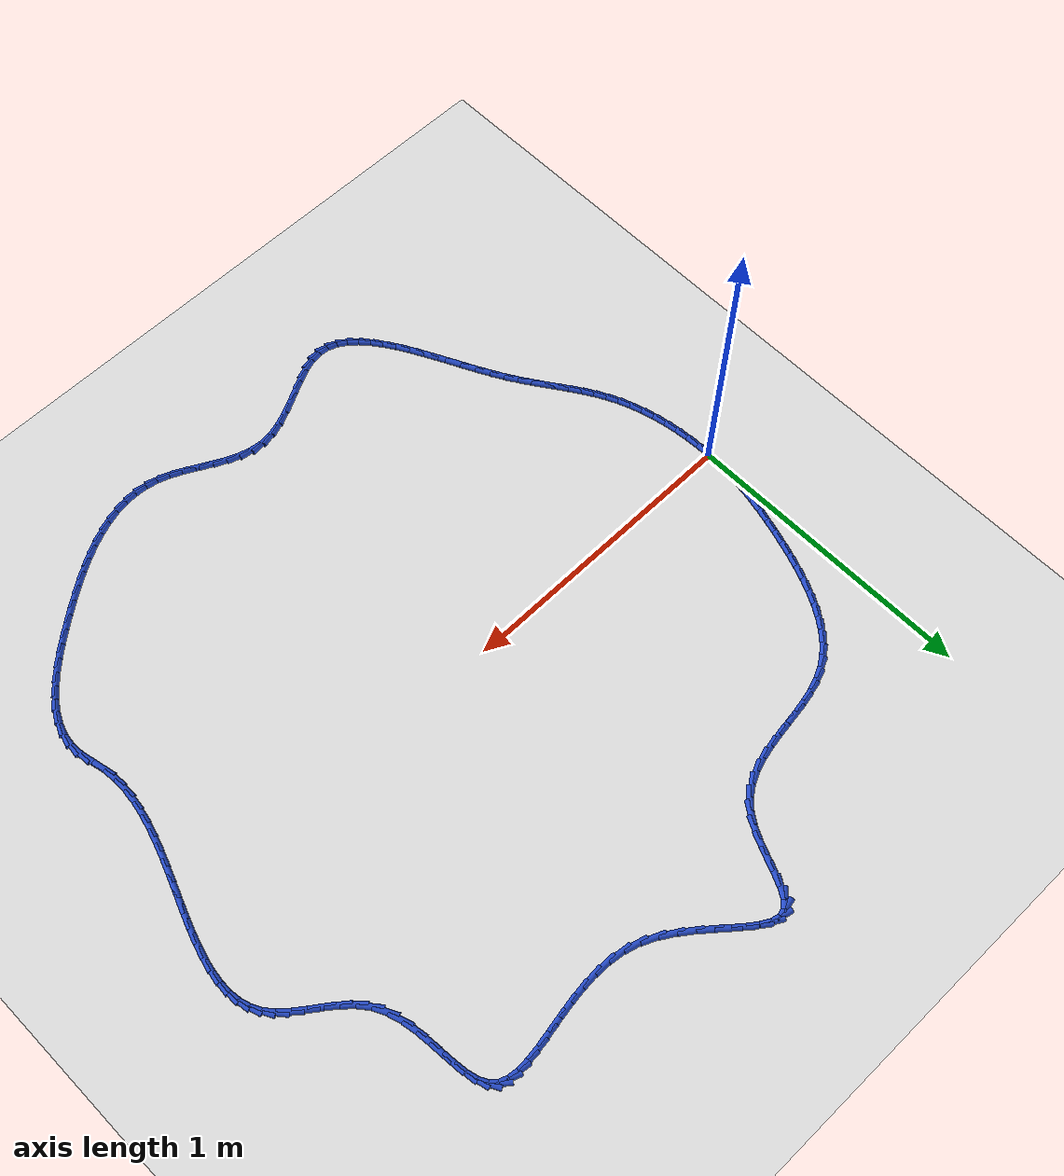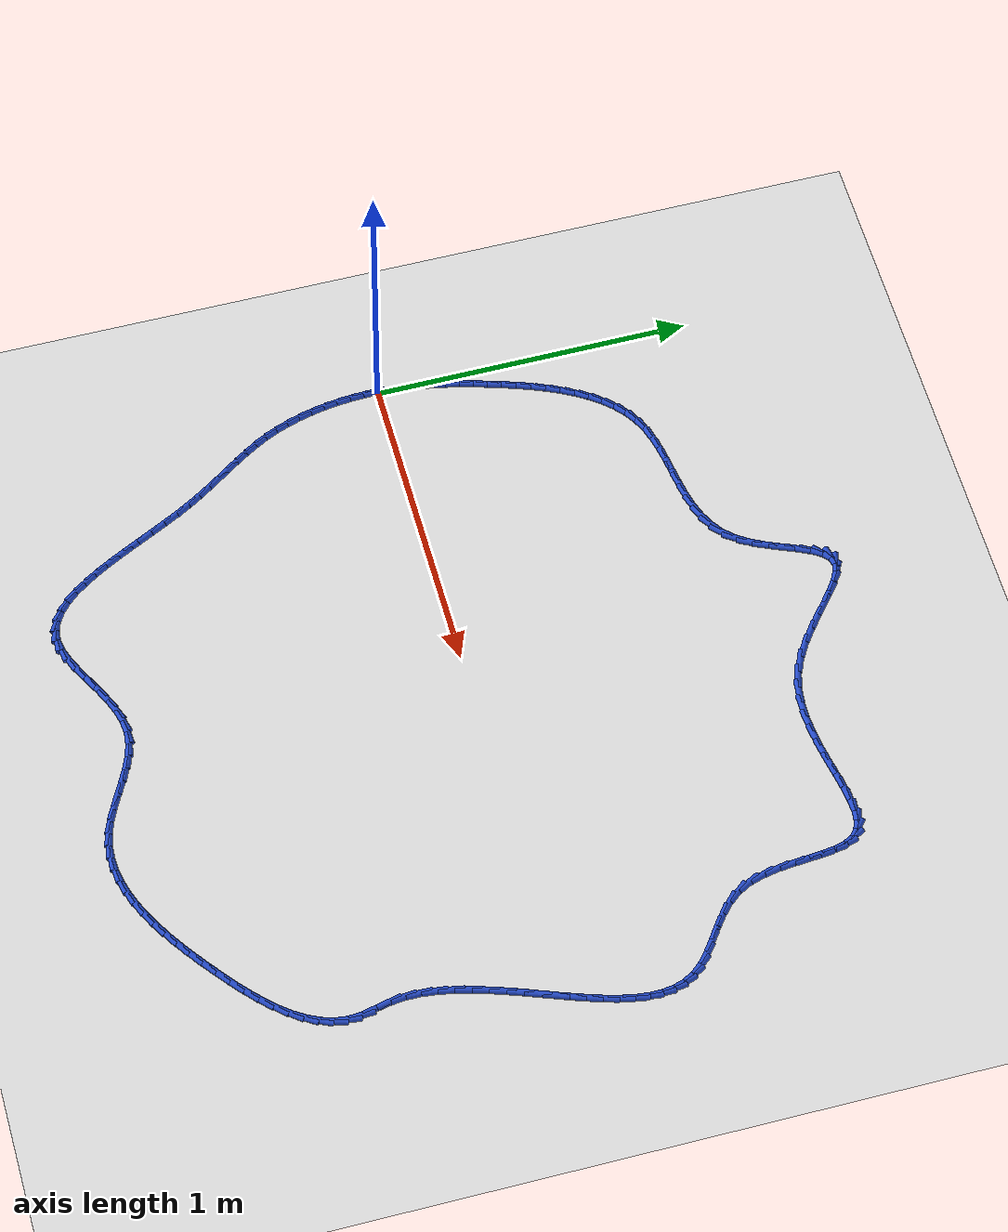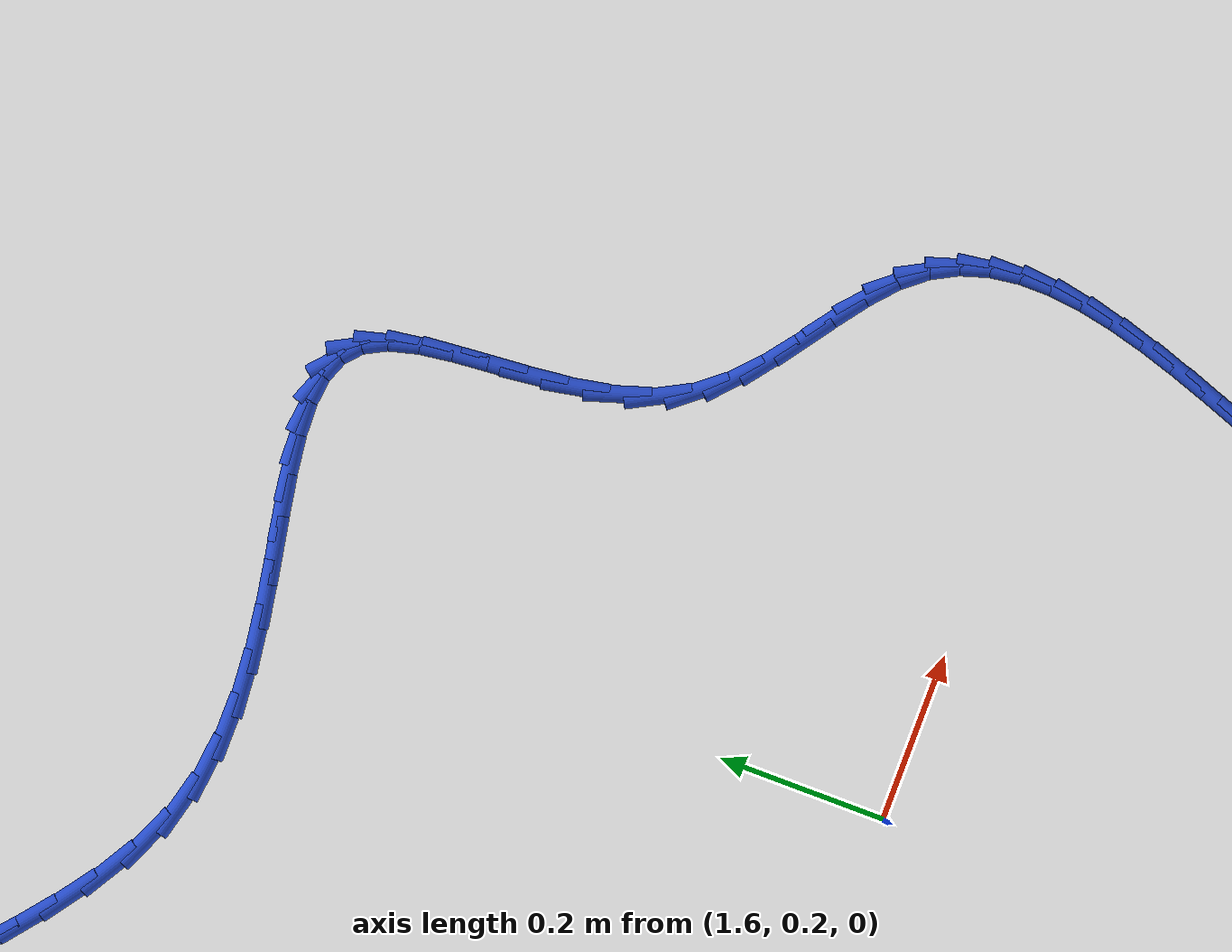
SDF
<sdf version="1.6">
 <world name="default">
  <light name="sun" type="directional">
   <pose>0 0 10 0 -0 0</pose>
   <diffuse>0.8 0.8 0.8 1</diffuse>
   <specular>0.2 0.2 0.2 1</specular>
   <attenuation>
    <range>1000</range>
    <constant>0.9</constant>
    <linear>0.01</linear>
    <quadratic>0.001</quadratic>
   </attenuation>
   <direction>-0.5 0.1 -0.9</direction>
  </light>
  <model name="ground_plane">
   <static>1</static>
   <link name="link">
    <collision name="collision">
     <geometry><plane><normal>0 0 1</normal><size>100 100</size></plane></geometry>
     <surface><friction><ode><mu>100</mu><mu2>50</mu2></ode></friction></surface>
    </collision>
    <visual name="visual">
     <cast_shadows>0</cast_shadows>
     <geometry><plane><normal>0 0 1</normal><size>100 100</size></plane></geometry>
     <material>
      <script><uri>file://media/materials/scripts/gazebo.material</uri><name>Gazebo/WhiteGlow</name></script>
     </material>
    </visual>
   </link>
  </model>
  <gravity>0 0 -9.8</gravity>
  <magnetic_field>6e-06 2.3e-05 -4.2e-05</magnetic_field>
  <atmosphere type="adiabatic"/>
  <physics name="default_physics" default="0" type="ode">
   <max_step_size>0.001</max_step_size>
   <real_time_factor>1</real_time_factor>
   <real_time_update_rate>1000</real_time_update_rate>
  </physics>
  <scene><ambient>0.4 0.4 0.4 1</ambient><background>0.7 0.7 0.7 1</background><shadows>1</shadows></scene>
  <spherical_coordinates>
   <surface_model>EARTH_WGS84</surface_model>
   <latitude_deg>0</latitude_deg>
   <longitude_deg>0</longitude_deg>
   <elevation>0</elevation>
   <heading_deg>0</heading_deg>
  </spherical_coordinates>
  <model name="line">
   <link name="link_0">
    <pose>0.0 2.0816681711721685e-17 0.01 0 1.57 1.5274658303655457</pose>
    <collision name="collision">
     <geometry><cylinder><radius>0.01</radius><length>0.08</length></cylinder></geometry>
    </collision>
    <visual name="visual">
     <material>
      <script><name>Gazebo/Blue</name><uri>file://media/materials/scripts/gazebo.material</uri></script>
     </material>
     <geometry><cylinder><radius>0.01</radius><length>0.08</length></cylinder></geometry>
    </visual>
   </link>
   <link name="link_1">
    <pose>0.001882932050623325 0.04342792343694653 0.01 0 1.57 1.4830346264562566</pose>
    <collision name="collision">
     <geometry><cylinder><radius>0.01</radius><length>0.08</length></cylinder></geometry>
    </collision>
    <visual name="visual">
     <material>
      <script><name>Gazebo/Blue</name><uri>file://media/materials/scripts/gazebo.material</uri></script>
     </material>
     <geometry><cylinder><radius>0.01</radius><length>0.08</length></cylinder></geometry>
    </visual>
   </link>
   <link name="link_2">
    <pose>0.005660563875606679 0.08636155212213174 0.01 0 1.57 1.441057252625302</pose>
    <collision name="collision">
     <geometry><cylinder><radius>0.01</radius><length>0.08</length></cylinder></geometry>
    </collision>
    <visual name="visual">
     <material>
      <script><name>Gazebo/Blue</name><uri>file://media/materials/scripts/gazebo.material</uri></script>
     </material>
     <geometry><cylinder><radius>0.01</radius><length>0.08</length></cylinder></geometry>
    </visual>
   </link>
   <link name="link_3">
    <pose>0.01121829659993773 0.12895870108899557 0.01 0 1.57 1.4021291156189073</pose>
    <collision name="collision">
     <geometry><cylinder><radius>0.01</radius><length>0.08</length></cylinder></geometry>
    </collision>
    <visual name="visual">
     <material>
      <script><name>Gazebo/Blue</name><uri>file://media/materials/scripts/gazebo.material</uri></script>
     </material>
     <geometry><cylinder><radius>0.01</radius><length>0.08</length></cylinder></geometry>
    </visual>
   </link>
   <link name="link_4">
    <pose>0.018441531348604167 0.17137718537097799 0.01 0 1.57 1.3667282829001004</pose>
    <collision name="collision">
     <geometry><cylinder><radius>0.01</radius><length>0.08</length></cylinder></geometry>
    </collision>
    <visual name="visual">
     <material>
      <script><name>Gazebo/Blue</name><uri>file://media/materials/scripts/gazebo.material</uri></script>
     </material>
     <geometry><cylinder><radius>0.01</radius><length>0.08</length></cylinder></geometry>
    </visual>
   </link>
   <link name="link_5">
    <pose>0.02721566924659366 0.21377482000151873 0.01 0 1.57 1.3352038154695058</pose>
    <collision name="collision">
     <geometry><cylinder><radius>0.01</radius><length>0.08</length></cylinder></geometry>
    </collision>
    <visual name="visual">
     <material>
      <script><name>Gazebo/Blue</name><uri>file://media/materials/scripts/gazebo.material</uri></script>
     </material>
     <geometry><cylinder><radius>0.01</radius><length>0.08</length></cylinder></geometry>
    </visual>
   </link>
   <link name="link_6">
    <pose>0.037426111418893904 0.2563094200140577 0.01 0 1.57 1.307776329983313</pose>
    <collision name="collision">
     <geometry><cylinder><radius>0.01</radius><length>0.08</length></cylinder></geometry>
    </collision>
    <visual name="visual">
     <material>
      <script><name>Gazebo/Blue</name><uri>file://media/materials/scripts/gazebo.material</uri></script>
     </material>
     <geometry><cylinder><radius>0.01</radius><length>0.08</length></cylinder></geometry>
    </visual>
   </link>
   <link name="link_7">
    <pose>0.04895825899049258 0.2991388004420349 0.01 0 1.57 1.2845479591983004</pose>
    <collision name="collision">
     <geometry><cylinder><radius>0.01</radius><length>0.08</length></cylinder></geometry>
    </collision>
    <visual name="visual">
     <material>
      <script><name>Gazebo/Blue</name><uri>file://media/materials/scripts/gazebo.material</uri></script>
     </material>
     <geometry><cylinder><radius>0.01</radius><length>0.08</length></cylinder></geometry>
    </visual>
   </link>
   <link name="link_8">
    <pose>0.06169751308637738 0.3424207763188901 0.01 0 1.57 1.2651666941944375</pose>
    <collision name="collision">
     <geometry><cylinder><radius>0.01</radius><length>0.08</length></cylinder></geometry>
    </collision>
    <visual name="visual">
     <material>
      <script><name>Gazebo/Blue</name><uri>file://media/materials/scripts/gazebo.material</uri></script>
     </material>
     <geometry><cylinder><radius>0.01</radius><length>0.08</length></cylinder></geometry>
    </visual>
   </link>
   <link name="link_9">
    <pose>0.07553934760905774 0.3862913273354509 0.01 0 1.57 1.2435836410821643</pose>
    <collision name="collision">
     <geometry><cylinder><radius>0.01</radius><length>0.08</length></cylinder></geometry>
    </collision>
    <visual name="visual">
     <material>
      <script><name>Gazebo/Blue</name><uri>file://media/materials/scripts/gazebo.material</uri></script>
     </material>
     <geometry><cylinder><radius>0.01</radius><length>0.08</length></cylinder></geometry>
    </visual>
   </link>
   <link name="link_10">
    <pose>0.09054993458861518 0.4305164009753659 0.01 0 1.57 1.2145333849777742</pose>
    <collision name="collision">
     <geometry><cylinder><radius>0.01</radius><length>0.08</length></cylinder></geometry>
    </collision>
    <visual name="visual">
     <material>
      <script><name>Gazebo/Blue</name><uri>file://media/materials/scripts/gazebo.material</uri></script>
     </material>
     <geometry><cylinder><radius>0.01</radius><length>0.08</length></cylinder></geometry>
    </visual>
   </link>
   <link name="link_11">
    <pose>0.1069378821469445 0.47455317776516853 0.01 0 1.57 1.1772221785938286</pose>
    <collision name="collision">
     <geometry><cylinder><radius>0.01</radius><length>0.08</length></cylinder></geometry>
    </collision>
    <visual name="visual">
     <material>
      <script><name>Gazebo/Blue</name><uri>file://media/materials/scripts/gazebo.material</uri></script>
     </material>
     <geometry><cylinder><radius>0.01</radius><length>0.08</length></cylinder></geometry>
    </visual>
   </link>
   <link name="link_12">
    <pose>0.12491616066155674 0.5178493819175072 0.01 0 1.57 1.130655671403392</pose>
    <collision name="collision">
     <geometry><cylinder><radius>0.01</radius><length>0.08</length></cylinder></geometry>
    </collision>
    <visual name="visual">
     <material>
      <script><name>Gazebo/Blue</name><uri>file://media/materials/scripts/gazebo.material</uri></script>
     </material>
     <geometry><cylinder><radius>0.01</radius><length>0.08</length></cylinder></geometry>
    </visual>
   </link>
   <link name="link_13">
    <pose>0.14469774050996284 0.5598527376450301 0.01 0 1.57 1.0734984498851592</pose>
    <collision name="collision">
     <geometry><cylinder><radius>0.01</radius><length>0.08</length></cylinder></geometry>
    </collision>
    <visual name="visual">
     <material>
      <script><name>Gazebo/Blue</name><uri>file://media/materials/scripts/gazebo.material</uri></script>
     </material>
     <geometry><cylinder><radius>0.01</radius><length>0.08</length></cylinder></geometry>
    </visual>
   </link>
   <link name="link_14">
    <pose>0.1664955920696738 0.6000109691603858 0.01 0 1.57 1.0041147316822503</pose>
    <collision name="collision">
     <geometry><cylinder><radius>0.01</radius><length>0.08</length></cylinder></geometry>
    </collision>
    <visual name="visual">
     <material>
      <script><name>Gazebo/Blue</name><uri>file://media/materials/scripts/gazebo.material</uri></script>
     </material>
     <geometry><cylinder><radius>0.01</radius><length>0.08</length></cylinder></geometry>
    </visual>
   </link>
   <link name="link_15">
    <pose>0.19052268571820058 0.6377718006762223 0.01 0 1.57 0.920692338920106</pose>
    <collision name="collision">
     <geometry><cylinder><radius>0.01</radius><length>0.08</length></cylinder></geometry>
    </collision>
    <visual name="visual">
     <material>
      <script><name>Gazebo/Blue</name><uri>file://media/materials/scripts/gazebo.material</uri></script>
     </material>
     <geometry><cylinder><radius>0.01</radius><length>0.08</length></cylinder></geometry>
    </visual>
   </link>
   <link name="link_16">
    <pose>0.21699199183305423 0.6725829564051883 0.01 0 1.57 0.8215330431041581</pose>
    <collision name="collision">
     <geometry><cylinder><radius>0.01</radius><length>0.08</length></cylinder></geometry>
    </collision>
    <visual name="visual">
     <material>
      <script><name>Gazebo/Blue</name><uri>file://media/materials/scripts/gazebo.material</uri></script>
     </material>
     <geometry><cylinder><radius>0.01</radius><length>0.08</length></cylinder></geometry>
    </visual>
   </link>
   <link name="link_17">
    <pose>0.24611648079174578 0.7038921605599324 0.01 0 1.57 0.7056041369689432</pose>
    <collision name="collision">
     <geometry><cylinder><radius>0.01</radius><length>0.08</length></cylinder></geometry>
    </collision>
    <visual name="visual">
     <material>
      <script><name>Gazebo/Blue</name><uri>file://media/materials/scripts/gazebo.material</uri></script>
     </material>
     <geometry><cylinder><radius>0.01</radius><length>0.08</length></cylinder></geometry>
    </visual>
   </link>
   <link name="link_18">
    <pose>0.278109122971786 0.7311471373531022 0.01 0 1.57 0.5733734565252111</pose>
    <collision name="collision">
     <geometry><cylinder><radius>0.01</radius><length>0.08</length></cylinder></geometry>
    </collision>
    <visual name="visual">
     <material>
      <script><name>Gazebo/Blue</name><uri>file://media/materials/scripts/gazebo.material</uri></script>
     </material>
     <geometry><cylinder><radius>0.01</radius><length>0.08</length></cylinder></geometry>
    </visual>
   </link>
   <link name="link_19">
    <pose>0.313182888750686 0.7537956109973463 0.01 0 1.57 0.43009340562347703</pose>
    <collision name="collision">
     <geometry><cylinder><radius>0.01</radius><length>0.08</length></cylinder></geometry>
    </collision>
    <visual name="visual">
     <material>
      <script><name>Gazebo/Blue</name><uri>file://media/materials/scripts/gazebo.material</uri></script>
     </material>
     <geometry><cylinder><radius>0.01</radius><length>0.08</length></cylinder></geometry>
    </visual>
   </link>
   <link name="link_20">
    <pose>0.35150315892209255 0.7713744248897481 0.01 0 1.57 0.3066090634197765</pose>
    <collision name="collision">
     <geometry><cylinder><radius>0.01</radius><length>0.08</length></cylinder></geometry>
    </collision>
    <visual name="visual">
     <material>
      <script><name>Gazebo/Blue</name><uri>file://media/materials/scripts/gazebo.material</uri></script>
     </material>
     <geometry><cylinder><radius>0.01</radius><length>0.08</length></cylinder></geometry>
    </visual>
   </link>
   <link name="link_21">
    <pose>0.39270266857234926 0.7844178875694007 0.01 0 1.57 0.21929909739808087</pose>
    <collision name="collision">
     <geometry><cylinder><radius>0.01</radius><length>0.08</length></cylinder></geometry>
    </collision>
    <visual name="visual">
     <material>
      <script><name>Gazebo/Blue</name><uri>file://media/materials/scripts/gazebo.material</uri></script>
     </material>
     <geometry><cylinder><radius>0.01</radius><length>0.08</length></cylinder></geometry>
    </visual>
   </link>
   <link name="link_22">
    <pose>0.43608003815203483 0.7940859912109586 0.01 0 1.57 0.16487985646915165</pose>
    <collision name="collision">
     <geometry><cylinder><radius>0.01</radius><length>0.08</length></cylinder></geometry>
    </collision>
    <visual name="visual">
     <material>
      <script><name>Gazebo/Blue</name><uri>file://media/materials/scripts/gazebo.material</uri></script>
     </material>
     <geometry><cylinder><radius>0.01</radius><length>0.08</length></cylinder></geometry>
    </visual>
   </link>
   <link name="link_23">
    <pose>0.4809287323590615 0.8015483829689165 0.01 0 1.57 0.13996535813844757</pose>
    <collision name="collision">
     <geometry><cylinder><radius>0.01</radius><length>0.08</length></cylinder></geometry>
    </collision>
    <visual name="visual">
     <material>
      <script><name>Gazebo/Blue</name><uri>file://media/materials/scripts/gazebo.material</uri></script>
     </material>
     <geometry><cylinder><radius>0.01</radius><length>0.08</length></cylinder></geometry>
    </visual>
   </link>
   <link name="link_24">
    <pose>0.5265422158913406 0.8079747099977692 0.01 0 1.57 0.1426560413136113</pose>
    <collision name="collision">
     <geometry><cylinder><radius>0.01</radius><length>0.08</length></cylinder></geometry>
    </collision>
    <visual name="visual">
     <material>
      <script><name>Gazebo/Blue</name><uri>file://media/materials/scripts/gazebo.material</uri></script>
     </material>
     <geometry><cylinder><radius>0.01</radius><length>0.08</length></cylinder></geometry>
    </visual>
   </link>
   <link name="link_25">
    <pose>0.5722139534467843 0.8145346194520118 0.01 0 1.57 0.1729015719749586</pose>
    <collision name="collision">
     <geometry><cylinder><radius>0.01</radius><length>0.08</length></cylinder></geometry>
    </collision>
    <visual name="visual">
     <material>
      <script><name>Gazebo/Blue</name><uri>file://media/materials/scripts/gazebo.material</uri></script>
     </material>
     <geometry><cylinder><radius>0.01</radius><length>0.08</length></cylinder></geometry>
    </visual>
   </link>
   <link name="link_26">
    <pose>0.6172374097233042 0.8223977584861387 0.01 0 1.57 0.2324147633976279</pose>
    <collision name="collision">
     <geometry><cylinder><radius>0.01</radius><length>0.08</length></cylinder></geometry>
    </collision>
    <visual name="visual">
     <material>
      <script><name>Gazebo/Blue</name><uri>file://media/materials/scripts/gazebo.material</uri></script>
     </material>
     <geometry><cylinder><radius>0.01</radius><length>0.08</length></cylinder></geometry>
    </visual>
   </link>
   <link name="link_27">
    <pose>0.6609060494188117 0.8327337742546448 0.01 0 1.57 0.3241160413838412</pose>
    <collision name="collision">
     <geometry><cylinder><radius>0.01</radius><length>0.08</length></cylinder></geometry>
    </collision>
    <visual name="visual">
     <material>
      <script><name>Gazebo/Blue</name><uri>file://media/materials/scripts/gazebo.material</uri></script>
     </material>
     <geometry><cylinder><radius>0.01</radius><length>0.08</length></cylinder></geometry>
    </visual>
   </link>
   <link name="link_28">
    <pose>0.7025133372312192 0.8467123139120253 0.01 0 1.57 0.45060817402634884</pose>
    <collision name="collision">
     <geometry><cylinder><radius>0.01</radius><length>0.08</length></cylinder></geometry>
    </collision>
    <visual name="visual">
     <material>
      <script><name>Gazebo/Blue</name><uri>file://media/materials/scripts/gazebo.material</uri></script>
     </material>
     <geometry><cylinder><radius>0.01</radius><length>0.08</length></cylinder></geometry>
    </visual>
   </link>
   <link name="link_29">
    <pose>0.7413527378584385 0.865503024612775 0.01 0 1.57 0.6110493484713455</pose>
    <collision name="collision">
     <geometry><cylinder><radius>0.01</radius><length>0.08</length></cylinder></geometry>
    </collision>
    <visual name="visual">
     <material>
      <script><name>Gazebo/Blue</name><uri>file://media/materials/scripts/gazebo.material</uri></script>
     </material>
     <geometry><cylinder><radius>0.01</radius><length>0.08</length></cylinder></geometry>
    </visual>
   </link>
   <link name="link_30">
    <pose>0.7767177159983806 0.8902755535113882 0.01 0 1.57 0.7971231399385907</pose>
    <collision name="collision">
     <geometry><cylinder><radius>0.01</radius><length>0.08</length></cylinder></geometry>
    </collision>
    <visual name="visual">
     <material>
      <script><name>Gazebo/Blue</name><uri>file://media/materials/scripts/gazebo.material</uri></script>
     </material>
     <geometry><cylinder><radius>0.01</radius><length>0.08</length></cylinder></geometry>
    </visual>
   </link>
   <link name="link_31">
    <pose>0.8079017363489582 0.9221995477623603 0.01 0 1.57 0.9794834374040592</pose>
    <collision name="collision">
     <geometry><cylinder><radius>0.01</radius><length>0.08</length></cylinder></geometry>
    </collision>
    <visual name="visual">
     <material>
      <script><name>Gazebo/Blue</name><uri>file://media/materials/scripts/gazebo.material</uri></script>
     </material>
     <geometry><cylinder><radius>0.01</radius><length>0.08</length></cylinder></geometry>
    </visual>
   </link>
   <link name="link_32">
    <pose>0.8344759133729378 0.9617763284519439 0.01 0 1.57 1.0992245112673753</pose>
    <collision name="collision">
     <geometry><cylinder><radius>0.01</radius><length>0.08</length></cylinder></geometry>
    </collision>
    <visual name="visual">
     <material>
      <script><name>Gazebo/Blue</name><uri>file://media/materials/scripts/gazebo.material</uri></script>
     </material>
     <geometry><cylinder><radius>0.01</radius><length>0.08</length></cylinder></geometry>
    </visual>
   </link>
   <link name="link_33">
    <pose>0.8572704856351552 1.0064764002671658 0.01 0 1.57 1.1604379181783198</pose>
    <collision name="collision">
     <geometry><cylinder><radius>0.01</radius><length>0.08</length></cylinder></geometry>
    </collision>
    <visual name="visual">
     <material>
      <script><name>Gazebo/Blue</name><uri>file://media/materials/scripts/gazebo.material</uri></script>
     </material>
     <geometry><cylinder><radius>0.01</radius><length>0.08</length></cylinder></geometry>
    </visual>
   </link>
   <link name="link_34">
    <pose>0.877472439163415 1.0529115470911425 0.01 0 1.57 1.1733975695237424</pose>
    <collision name="collision">
     <geometry><cylinder><radius>0.01</radius><length>0.08</length></cylinder></geometry>
    </collision>
    <visual name="visual">
     <material>
      <script><name>Gazebo/Blue</name><uri>file://media/materials/scripts/gazebo.material</uri></script>
     </material>
     <geometry><cylinder><radius>0.01</radius><length>0.08</length></cylinder></geometry>
    </visual>
   </link>
   <link name="link_35">
    <pose>0.8962687830290101 1.0976934973393997 0.01 0 1.57 1.133504327110469</pose>
    <collision name="collision">
     <geometry><cylinder><radius>0.01</radius><length>0.08</length></cylinder></geometry>
    </collision>
    <visual name="visual">
     <material>
      <script><name>Gazebo/Blue</name><uri>file://media/materials/scripts/gazebo.material</uri></script>
     </material>
     <geometry><cylinder><radius>0.01</radius><length>0.08</length></cylinder></geometry>
    </visual>
   </link>
   <link name="link_36">
    <pose>0.9148465263032342 1.1374339794274633 0.01 0 1.57 1.012726847234206</pose>
    <collision name="collision">
     <geometry><cylinder><radius>0.01</radius><length>0.08</length></cylinder></geometry>
    </collision>
    <visual name="visual">
     <material>
      <script><name>Gazebo/Blue</name><uri>file://media/materials/scripts/gazebo.material</uri></script>
     </material>
     <geometry><cylinder><radius>0.01</radius><length>0.08</length></cylinder></geometry>
    </visual>
   </link>
   <link name="link_37">
    <pose>0.9343926780573804 1.1687447217708578 0.01 0 1.57 0.7318304570410479</pose>
    <collision name="collision">
     <geometry><cylinder><radius>0.01</radius><length>0.08</length></cylinder></geometry>
    </collision>
    <visual name="visual">
     <material>
      <script><name>Gazebo/Blue</name><uri>file://media/materials/scripts/gazebo.material</uri></script>
     </material>
     <geometry><cylinder><radius>0.01</radius><length>0.08</length></cylinder></geometry>
    </visual>
   </link>
   <link name="link_38">
    <pose>0.9560942400626891 1.1882374851318345 0.01 0 1.57 0.21242757763754652</pose>
    <collision name="collision">
     <geometry><cylinder><radius>0.01</radius><length>0.08</length></cylinder></geometry>
    </collision>
    <visual name="visual">
     <material>
      <script><name>Gazebo/Blue</name><uri>file://media/materials/scripts/gazebo.material</uri></script>
     </material>
     <geometry><cylinder><radius>0.01</radius><length>0.08</length></cylinder></geometry>
    </visual>
   </link>
   <link name="link_39">
    <pose>0.9808982636227594 1.1935872572387711 0.01 0 1.57 -0.25374595940826594</pose>
    <collision name="collision">
     <geometry><cylinder><radius>0.01</radius><length>0.08</length></cylinder></geometry>
    </collision>
    <visual name="visual">
     <material>
      <script><name>Gazebo/Blue</name><uri>file://media/materials/scripts/gazebo.material</uri></script>
     </material>
     <geometry><cylinder><radius>0.01</radius><length>0.08</length></cylinder></geometry>
    </visual>
   </link>
   <link name="link_40">
    <pose>1.0088803375806383 1.1863304993863466 0.01 0 1.57 -0.5121843927509631</pose>
    <collision name="collision">
     <geometry><cylinder><radius>0.01</radius><length>0.08</length></cylinder></geometry>
    </collision>
    <visual name="visual">
     <material>
      <script><name>Gazebo/Blue</name><uri>file://media/materials/scripts/gazebo.material</uri></script>
     </material>
     <geometry><cylinder><radius>0.01</radius><length>0.08</length></cylinder></geometry>
    </visual>
   </link>
   <link name="link_41">
    <pose>1.0399182711945005 1.1688800395212853 0.01 0 1.57 -0.6388245669623184</pose>
    <collision name="collision">
     <geometry><cylinder><radius>0.01</radius><length>0.08</length></cylinder></geometry>
    </collision>
    <visual name="visual">
     <material>
      <script><name>Gazebo/Blue</name><uri>file://media/materials/scripts/gazebo.material</uri></script>
     </material>
     <geometry><cylinder><radius>0.01</radius><length>0.08</length></cylinder></geometry>
    </visual>
   </link>
   <link name="link_42">
    <pose>1.0738898737225218 1.1436487055903097 0.01 0 1.57 -0.6938843102755509</pose>
    <collision name="collision">
     <geometry><cylinder><radius>0.01</radius><length>0.08</length></cylinder></geometry>
    </collision>
    <visual name="visual">
     <material>
      <script><name>Gazebo/Blue</name><uri>file://media/materials/scripts/gazebo.material</uri></script>
     </material>
     <geometry><cylinder><radius>0.01</radius><length>0.08</length></cylinder></geometry>
    </visual>
   </link>
   <link name="link_43">
    <pose>1.1106729544228775 1.1130493255401448 0.01 0 1.57 -0.7045394406214696</pose>
    <collision name="collision">
     <geometry><cylinder><radius>0.01</radius><length>0.08</length></cylinder></geometry>
    </collision>
    <visual name="visual">
     <material>
      <script><name>Gazebo/Blue</name><uri>file://media/materials/scripts/gazebo.material</uri></script>
     </material>
     <geometry><cylinder><radius>0.01</radius><length>0.08</length></cylinder></geometry>
    </visual>
   </link>
   <link name="link_44">
    <pose>1.1501453225537421 1.079494727317513 0.01 0 1.57 -0.6814551570017929</pose>
    <collision name="collision">
     <geometry><cylinder><radius>0.01</radius><length>0.08</length></cylinder></geometry>
    </collision>
    <visual name="visual">
     <material>
      <script><name>Gazebo/Blue</name><uri>file://media/materials/scripts/gazebo.material</uri></script>
     </material>
     <geometry><cylinder><radius>0.01</radius><length>0.08</length></cylinder></geometry>
    </visual>
   </link>
   <link name="link_45">
    <pose>1.1921847873732925 1.0453977388691387 0.01 0 1.57 -0.6269453539872679</pose>
    <collision name="collision">
     <geometry><cylinder><radius>0.01</radius><length>0.08</length></cylinder></geometry>
    </collision>
    <visual name="visual">
     <material>
      <script><name>Gazebo/Blue</name><uri>file://media/materials/scripts/gazebo.material</uri></script>
     </material>
     <geometry><cylinder><radius>0.01</radius><length>0.08</length></cylinder></geometry>
    </visual>
   </link>
   <link name="link_46">
    <pose>1.2366691581397022 1.0131711881417453 0.01 0 1.57 -0.5382021097787669</pose>
    <collision name="collision">
     <geometry><cylinder><radius>0.01</radius><length>0.08</length></cylinder></geometry>
    </collision>
    <visual name="visual">
     <material>
      <script><name>Gazebo/Blue</name><uri>file://media/materials/scripts/gazebo.material</uri></script>
     </material>
     <geometry><cylinder><radius>0.01</radius><length>0.08</length></cylinder></geometry>
    </visual>
   </link>
   <link name="link_47">
    <pose>1.283476244111149 0.9852279030820568 0.01 0 1.57 -0.4091280359965647</pose>
    <collision name="collision">
     <geometry><cylinder><radius>0.01</radius><length>0.08</length></cylinder></geometry>
    </collision>
    <visual name="visual">
     <material>
      <script><name>Gazebo/Blue</name><uri>file://media/materials/scripts/gazebo.material</uri></script>
     </material>
     <geometry><cylinder><radius>0.01</radius><length>0.08</length></cylinder></geometry>
    </visual>
   </link>
   <link name="link_48">
    <pose>1.3324835380963123 0.9639785895958195 0.01 0 1.57 -0.25166430734247897</pose>
    <collision name="collision">
     <geometry><cylinder><radius>0.01</radius><length>0.08</length></cylinder></geometry>
    </collision>
    <visual name="visual">
     <material>
      <script><name>Gazebo/Blue</name><uri>file://media/materials/scripts/gazebo.material</uri></script>
     </material>
     <geometry><cylinder><radius>0.01</radius><length>0.08</length></cylinder></geometry>
    </visual>
   </link>
   <link name="link_49">
    <pose>1.383426335216906 0.9508804070509274 0.01 0 1.57 -0.11327274444445434</pose>
    <collision name="collision">
     <geometry><cylinder><radius>0.01</radius><length>0.08</length></cylinder></geometry>
    </collision>
    <visual name="visual">
     <material>
      <script><name>Gazebo/Blue</name><uri>file://media/materials/scripts/gazebo.material</uri></script>
     </material>
     <geometry><cylinder><radius>0.01</radius><length>0.08</length></cylinder></geometry>
    </visual>
   </link>
   <link name="link_50">
    <pose>1.4356740093759344 0.9449367272842448 0.01 0 1.57 -0.0033122318061383446</pose>
    <collision name="collision">
     <geometry><cylinder><radius>0.01</radius><length>0.08</length></cylinder></geometry>
    </collision>
    <visual name="visual">
     <material>
      <script><name>Gazebo/Blue</name><uri>file://media/materials/scripts/gazebo.material</uri></script>
     </material>
     <geometry><cylinder><radius>0.01</radius><length>0.08</length></cylinder></geometry>
    </visual>
   </link>
   <link name="link_51">
    <pose>1.4885378811504482 0.9447616292464307 0.01 0 1.57 0.07953355903179206</pose>
    <collision name="collision">
     <geometry><cylinder><radius>0.01</radius><length>0.08</length></cylinder></geometry>
    </collision>
    <visual name="visual">
     <material>
      <script><name>Gazebo/Blue</name><uri>file://media/materials/scripts/gazebo.material</uri></script>
     </material>
     <geometry><cylinder><radius>0.01</radius><length>0.08</length></cylinder></geometry>
    </visual>
   </link>
   <link name="link_52">
    <pose>1.5413292711175002 0.9489691918881434 0.01 0 1.57 0.13758893823305643</pose>
    <collision name="collision">
     <geometry><cylinder><radius>0.01</radius><length>0.08</length></cylinder></geometry>
    </collision>
    <visual name="visual">
     <material>
      <script><name>Gazebo/Blue</name><uri>file://media/materials/scripts/gazebo.material</uri></script>
     </material>
     <geometry><cylinder><radius>0.01</radius><length>0.08</length></cylinder></geometry>
    </visual>
   </link>
   <link name="link_53">
    <pose>1.5933594998541412 0.9561734941600414 0.01 0 1.57 0.1725464159879727</pose>
    <collision name="collision">
     <geometry><cylinder><radius>0.01</radius><length>0.08</length></cylinder></geometry>
    </collision>
    <visual name="visual">
     <material>
      <script><name>Gazebo/Blue</name><uri>file://media/materials/scripts/gazebo.material</uri></script>
     </material>
     <geometry><cylinder><radius>0.01</radius><length>0.08</length></cylinder></geometry>
    </visual>
   </link>
   <link name="link_54">
    <pose>1.6439398879374234 0.9649886150127829 0.01 0 1.57 0.1844936514445107</pose>
    <collision name="collision">
     <geometry><cylinder><radius>0.01</radius><length>0.08</length></cylinder></geometry>
    </collision>
    <visual name="visual">
     <material>
      <script><name>Gazebo/Blue</name><uri>file://media/materials/scripts/gazebo.material</uri></script>
     </material>
     <geometry><cylinder><radius>0.01</radius><length>0.08</length></cylinder></geometry>
    </visual>
   </link>
   <link name="link_55">
    <pose>1.6923817559443992 0.9740286333970268 0.01 0 1.57 0.171041702690649</pose>
    <collision name="collision">
     <geometry><cylinder><radius>0.01</radius><length>0.08</length></cylinder></geometry>
    </collision>
    <visual name="visual">
     <material>
      <script><name>Gazebo/Blue</name><uri>file://media/materials/scripts/gazebo.material</uri></script>
     </material>
     <geometry><cylinder><radius>0.01</radius><length>0.08</length></cylinder></geometry>
    </visual>
   </link>
   <link name="link_56">
    <pose>1.7379964244521195 0.9819076282634314 0.01 0 1.57 0.12598485674907975</pose>
    <collision name="collision">
     <geometry><cylinder><radius>0.01</radius><length>0.08</length></cylinder></geometry>
    </collision>
    <visual name="visual">
     <material>
      <script><name>Gazebo/Blue</name><uri>file://media/materials/scripts/gazebo.material</uri></script>
     </material>
     <geometry><cylinder><radius>0.01</radius><length>0.08</length></cylinder></geometry>
    </visual>
   </link>
   <link name="link_57">
    <pose>1.7800952140376363 0.9872396785626548 0.01 0 1.57 0.03690665576698272</pose>
    <collision name="collision">
     <geometry><cylinder><radius>0.01</radius><length>0.08</length></cylinder></geometry>
    </collision>
    <visual name="visual">
     <material>
      <script><name>Gazebo/Blue</name><uri>file://media/materials/scripts/gazebo.material</uri></script>
     </material>
     <geometry><cylinder><radius>0.01</radius><length>0.08</length></cylinder></geometry>
    </visual>
   </link>
   <link name="link_58">
    <pose>1.8179894452780023 0.9886388632453561 0.01 0 1.57 -0.11821842154475909</pose>
    <collision name="collision">
     <geometry><cylinder><radius>0.01</radius><length>0.08</length></cylinder></geometry>
    </collision>
    <visual name="visual">
     <material>
      <script><name>Gazebo/Blue</name><uri>file://media/materials/scripts/gazebo.material</uri></script>
     </material>
     <geometry><cylinder><radius>0.01</radius><length>0.08</length></cylinder></geometry>
    </visual>
   </link>
   <link name="link_59">
    <pose>1.850990438750268 0.9847192612621934 0.01 0 1.57 -0.36966582225953754</pose>
    <collision name="collision">
     <geometry><cylinder><radius>0.01</radius><length>0.08</length></cylinder></geometry>
    </collision>
    <visual name="visual">
     <material>
      <script><name>Gazebo/Blue</name><uri>file://media/materials/scripts/gazebo.material</uri></script>
     </material>
     <geometry><cylinder><radius>0.01</radius><length>0.08</length></cylinder></geometry>
    </visual>
   </link>
   <link name="link_60">
    <pose>1.8784095150314855 0.9740949515638251 0.01 0 1.57 -0.7244268516821153</pose>
    <collision name="collision">
     <geometry><cylinder><radius>0.01</radius><length>0.08</length></cylinder></geometry>
    </collision>
    <visual name="visual">
     <material>
      <script><name>Gazebo/Blue</name><uri>file://media/materials/scripts/gazebo.material</uri></script>
     </material>
     <geometry><cylinder><radius>0.01</radius><length>0.08</length></cylinder></geometry>
    </visual>
   </link>
   <link name="link_61">
    <pose>1.8995579946987076 0.95538001310091 0.01 0 1.57 -1.0883251237576683</pose>
    <collision name="collision">
     <geometry><cylinder><radius>0.01</radius><length>0.08</length></cylinder></geometry>
    </collision>
    <visual name="visual">
     <material>
      <script><name>Gazebo/Blue</name><uri>file://media/materials/scripts/gazebo.material</uri></script>
     </material>
     <geometry><cylinder><radius>0.01</radius><length>0.08</length></cylinder></geometry>
    </visual>
   </link>
   <link name="link_62">
    <pose>1.9140900778833903 0.927634103928793 0.01 0 1.57 -1.317982371278395</pose>
    <collision name="collision">
     <geometry><cylinder><radius>0.01</radius><length>0.08</length></cylinder></geometry>
    </collision>
    <visual name="visual">
     <material>
      <script><name>Gazebo/Blue</name><uri>file://media/materials/scripts/gazebo.material</uri></script>
     </material>
     <geometry><cylinder><radius>0.01</radius><length>0.08</length></cylinder></geometry>
    </visual>
   </link>
   <link name="link_63">
    <pose>1.9232875789545103 0.8920320006201256 0.01 0 1.57 -1.43652399251131</pose>
    <collision name="collision">
     <geometry><cylinder><radius>0.01</radius><length>0.08</length></cylinder></geometry>
    </collision>
    <visual name="visual">
     <material>
      <script><name>Gazebo/Blue</name><uri>file://media/materials/scripts/gazebo.material</uri></script>
     </material>
     <geometry><cylinder><radius>0.01</radius><length>0.08</length></cylinder></geometry>
    </visual>
   </link>
   <link name="link_64">
    <pose>1.9289147618509568 0.8503754329871352 0.01 0 1.57 -1.4877537974794481</pose>
    <collision name="collision">
     <geometry><cylinder><radius>0.01</radius><length>0.08</length></cylinder></geometry>
    </collision>
    <visual name="visual">
     <material>
      <script><name>Gazebo/Blue</name><uri>file://media/materials/scripts/gazebo.material</uri></script>
     </material>
     <geometry><cylinder><radius>0.01</radius><length>0.08</length></cylinder></geometry>
    </visual>
   </link>
   <link name="link_65">
    <pose>1.9327359660613794 0.8044662290205316 0.01 0 1.57 -1.4928001165012166</pose>
    <collision name="collision">
     <geometry><cylinder><radius>0.01</radius><length>0.08</length></cylinder></geometry>
    </collision>
    <visual name="visual">
     <material>
      <script><name>Gazebo/Blue</name><uri>file://media/materials/scripts/gazebo.material</uri></script>
     </material>
     <geometry><cylinder><radius>0.01</radius><length>0.08</length></cylinder></geometry>
    </visual>
   </link>
   <link name="link_66">
    <pose>1.936515531074427 0.7561062167110235 0.01 0 1.57 -1.4589939777825072</pose>
    <collision name="collision">
     <geometry><cylinder><radius>0.01</radius><length>0.08</length></cylinder></geometry>
    </collision>
    <visual name="visual">
     <material>
      <script><name>Gazebo/Blue</name><uri>file://media/materials/scripts/gazebo.material</uri></script>
     </material>
     <geometry><cylinder><radius>0.01</radius><length>0.08</length></cylinder></geometry>
    </visual>
   </link>
   <link name="link_67">
    <pose>1.9420177963787506 0.7070972240493215 0.01 0 1.57 -1.3851198068951116</pose>
    <collision name="collision">
     <geometry><cylinder><radius>0.01</radius><length>0.08</length></cylinder></geometry>
    </collision>
    <visual name="visual">
     <material>
      <script><name>Gazebo/Blue</name><uri>file://media/materials/scripts/gazebo.material</uri></script>
     </material>
     <geometry><cylinder><radius>0.01</radius><length>0.08</length></cylinder></geometry>
    </visual>
   </link>
   <link name="link_68">
    <pose>1.9510071014629975 0.6592410790261337 0.01 0 1.57 -1.2636770756298876</pose>
    <collision name="collision">
     <geometry><cylinder><radius>0.01</radius><length>0.08</length></cylinder></geometry>
    </collision>
    <visual name="visual">
     <material>
      <script><name>Gazebo/Blue</name><uri>file://media/materials/scripts/gazebo.material</uri></script>
     </material>
     <geometry><cylinder><radius>0.01</radius><length>0.08</length></cylinder></geometry>
    </visual>
   </link>
   <link name="link_69">
    <pose>1.9652477858158182 0.6143396096321709 0.01 0 1.57 -1.084621143090298</pose>
    <collision name="collision">
     <geometry><cylinder><radius>0.01</radius><length>0.08</length></cylinder></geometry>
    </collision>
    <visual name="visual">
     <material>
      <script><name>Gazebo/Blue</name><uri>file://media/materials/scripts/gazebo.material</uri></script>
     </material>
     <geometry><cylinder><radius>0.01</radius><length>0.08</length></cylinder></geometry>
    </visual>
   </link>
   <link name="link_70">
    <pose>1.9864753520570495 0.5741727918247984 0.01 0 1.57 -0.8868587768854662</pose>
    <collision name="collision">
     <geometry><cylinder><radius>0.01</radius><length>0.08</length></cylinder></geometry>
    </collision>
    <visual name="visual">
     <material>
      <script><name>Gazebo/Blue</name><uri>file://media/materials/scripts/gazebo.material</uri></script>
     </material>
     <geometry><cylinder><radius>0.01</radius><length>0.08</length></cylinder></geometry>
    </visual>
   </link>
   <link name="link_71">
    <pose>2.0148695110840564 0.5393416520430898 0.01 0 1.57 -0.7421211795983205</pose>
    <collision name="collision">
     <geometry><cylinder><radius>0.01</radius><length>0.08</length></cylinder></geometry>
    </collision>
    <visual name="visual">
     <material>
      <script><name>Gazebo/Blue</name><uri>file://media/materials/scripts/gazebo.material</uri></script>
     </material>
     <geometry><cylinder><radius>0.01</radius><length>0.08</length></cylinder></geometry>
    </visual>
   </link>
   <link name="link_72">
    <pose>2.0482937746032377 0.5086920448216737 0.01 0 1.57 -0.6552302108152249</pose>
    <collision name="collision">
     <geometry><cylinder><radius>0.01</radius><length>0.08</length></cylinder></geometry>
    </collision>
    <visual name="visual">
     <material>
      <script><name>Gazebo/Blue</name><uri>file://media/materials/scripts/gazebo.material</uri></script>
     </material>
     <geometry><cylinder><radius>0.01</radius><length>0.08</length></cylinder></geometry>
    </visual>
   </link>
   <link name="link_73">
    <pose>2.0844231456104207 0.4809269763625156 0.01 0 1.57 -0.622048552058305</pose>
    <collision name="collision">
     <geometry><cylinder><radius>0.01</radius><length>0.08</length></cylinder></geometry>
    </collision>
    <visual name="visual">
     <material>
      <script><name>Gazebo/Blue</name><uri>file://media/materials/scripts/gazebo.material</uri></script>
     </material>
     <geometry><cylinder><radius>0.01</radius><length>0.08</length></cylinder></geometry>
    </visual>
   </link>
   <link name="link_74">
    <pose>2.120932627101432 0.454749452867581 0.01 0 1.57 -0.6428254138603439</pose>
    <collision name="collision">
     <geometry><cylinder><radius>0.01</radius><length>0.08</length></cylinder></geometry>
    </collision>
    <visual name="visual">
     <material>
      <script><name>Gazebo/Blue</name><uri>file://media/materials/scripts/gazebo.material</uri></script>
     </material>
     <geometry><cylinder><radius>0.01</radius><length>0.08</length></cylinder></geometry>
    </visual>
   </link>
   <link name="link_75">
    <pose>2.155497222072098 0.4288624805388369 0.01 0 1.57 -0.7259925722121439</pose>
    <collision name="collision">
     <geometry><cylinder><radius>0.01</radius><length>0.08</length></cylinder></geometry>
    </collision>
    <visual name="visual">
     <material>
      <script><name>Gazebo/Blue</name><uri>file://media/materials/scripts/gazebo.material</uri></script>
     </material>
     <geometry><cylinder><radius>0.01</radius><length>0.08</length></cylinder></geometry>
    </visual>
   </link>
   <link name="link_76">
    <pose>2.185791933518246 0.4019690655782486 0.01 0 1.57 -0.8846344320275756</pose>
    <collision name="collision">
     <geometry><cylinder><radius>0.01</radius><length>0.08</length></cylinder></geometry>
    </collision>
    <visual name="visual">
     <material>
      <script><name>Gazebo/Blue</name><uri>file://media/materials/scripts/gazebo.material</uri></script>
     </material>
     <geometry><cylinder><radius>0.01</radius><length>0.08</length></cylinder></geometry>
    </visual>
   </link>
   <link name="link_77">
    <pose>2.2096401245272124 0.37284697826691876 0.01 0 1.57 -1.0805330866239526</pose>
    <collision name="collision">
     <geometry><cylinder><radius>0.01</radius><length>0.08</length></cylinder></geometry>
    </collision>
    <visual name="visual">
     <material>
      <script><name>Gazebo/Blue</name><uri>file://media/materials/scripts/gazebo.material</uri></script>
     </material>
     <geometry><cylinder><radius>0.01</radius><length>0.08</length></cylinder></geometry>
    </visual>
   </link>
   <link name="link_78">
    <pose>2.226567356146768 0.3411317887277146 0.01 0 1.57 -1.269100141707435</pose>
    <collision name="collision">
     <geometry><cylinder><radius>0.01</radius><length>0.08</length></cylinder></geometry>
    </collision>
    <visual name="visual">
     <material>
      <script><name>Gazebo/Blue</name><uri>file://media/materials/scripts/gazebo.material</uri></script>
     </material>
     <geometry><cylinder><radius>0.01</radius><length>0.08</length></cylinder></geometry>
    </visual>
   </link>
   <link name="link_79">
    <pose>2.23718679689371 0.30700715228658404 0.01 0 1.57 -1.4356248867870882</pose>
    <collision name="collision">
     <geometry><cylinder><radius>0.01</radius><length>0.08</length></cylinder></geometry>
    </collision>
    <visual name="visual">
     <material>
      <script><name>Gazebo/Blue</name><uri>file://media/materials/scripts/gazebo.material</uri></script>
     </material>
     <geometry><cylinder><radius>0.01</radius><length>0.08</length></cylinder></geometry>
    </visual>
   </link>
   <link name="link_80">
    <pose>2.2421292724069573 0.2706656223394508 0.01 0 1.57 1.5680943463863122</pose>
    <collision name="collision">
     <geometry><cylinder><radius>0.01</radius><length>0.08</length></cylinder></geometry>
    </collision>
    <visual name="visual">
     <material>
      <script><name>Gazebo/Blue</name><uri>file://media/materials/scripts/gazebo.material</uri></script>
     </material>
     <geometry><cylinder><radius>0.01</radius><length>0.08</length></cylinder></geometry>
    </visual>
   </link>
   <link name="link_81">
    <pose>2.242025608325431 0.23229975228223762 0.01 0 1.57 1.4588474102108986</pose>
    <collision name="collision">
     <geometry><cylinder><radius>0.01</radius><length>0.08</length></cylinder></geometry>
    </collision>
    <visual name="visual">
     <material>
      <script><name>Gazebo/Blue</name><uri>file://media/materials/scripts/gazebo.material</uri></script>
     </material>
     <geometry><cylinder><radius>0.01</radius><length>0.08</length></cylinder></geometry>
    </visual>
   </link>
   <link name="link_82">
    <pose>2.2375066302880486 0.19210209551086718 0.01 0 1.57 1.374870081161405</pose>
    <collision name="collision">
     <geometry><cylinder><radius>0.01</radius><length>0.08</length></cylinder></geometry>
    </collision>
    <visual name="visual">
     <material>
      <script><name>Gazebo/Blue</name><uri>file://media/materials/scripts/gazebo.material</uri></script>
     </material>
     <geometry><cylinder><radius>0.01</radius><length>0.08</length></cylinder></geometry>
    </visual>
   </link>
   <link name="link_83">
    <pose>2.2292031639337306 0.15026520542126348 0.01 0 1.57 1.3120316218282255</pose>
    <collision name="collision">
     <geometry><cylinder><radius>0.01</radius><length>0.08</length></cylinder></geometry>
    </collision>
    <visual name="visual">
     <material>
      <script><name>Gazebo/Blue</name><uri>file://media/materials/scripts/gazebo.material</uri></script>
     </material>
     <geometry><cylinder><radius>0.01</radius><length>0.08</length></cylinder></geometry>
    </visual>
   </link>
   <link name="link_84">
    <pose>2.217746034901396 0.10698163540934882 0.01 0 1.57 1.266645042887573</pose>
    <collision name="collision">
     <geometry><cylinder><radius>0.01</radius><length>0.08</length></cylinder></geometry>
    </collision>
    <visual name="visual">
     <material>
      <script><name>Gazebo/Blue</name><uri>file://media/materials/scripts/gazebo.material</uri></script>
     </material>
     <geometry><cylinder><radius>0.01</radius><length>0.08</length></cylinder></geometry>
    </visual>
   </link>
   <link name="link_85">
    <pose>2.2037660688299647 0.062443938871047086 0.01 0 1.57 1.2358372292294637</pose>
    <collision name="collision">
     <geometry><cylinder><radius>0.01</radius><length>0.08</length></cylinder></geometry>
    </collision>
    <visual name="visual">
     <material>
      <script><name>Gazebo/Blue</name><uri>file://media/materials/scripts/gazebo.material</uri></script>
     </material>
     <geometry><cylinder><radius>0.01</radius><length>0.08</length></cylinder></geometry>
    </visual>
   </link>
   <link name="link_86">
    <pose>2.1878940913583556 0.016844669202280976 0.01 0 1.57 1.2175545746428462</pose>
    <collision name="collision">
     <geometry><cylinder><radius>0.01</radius><length>0.08</length></cylinder></geometry>
    </collision>
    <visual name="visual">
     <material>
      <script><name>Gazebo/Blue</name><uri>file://media/materials/scripts/gazebo.material</uri></script>
     </material>
     <geometry><cylinder><radius>0.01</radius><length>0.08</length></cylinder></geometry>
    </visual>
   </link>
   <link name="link_87">
    <pose>2.1707609281254885 -0.02962362020102635 0.01 0 1.57 1.2104600362849076</pose>
    <collision name="collision">
     <geometry><cylinder><radius>0.01</radius><length>0.08</length></cylinder></geometry>
    </collision>
    <visual name="visual">
     <material>
      <script><name>Gazebo/Blue</name><uri>file://media/materials/scripts/gazebo.material</uri></script>
     </material>
     <geometry><cylinder><radius>0.01</radius><length>0.08</length></cylinder></geometry>
    </visual>
   </link>
   <link name="link_88">
    <pose>2.1529974047702827 -0.07676837594295186 0.01 0 1.57 1.2138251250247771</pose>
    <collision name="collision">
     <geometry><cylinder><radius>0.01</radius><length>0.08</length></cylinder></geometry>
    </collision>
    <visual name="visual">
     <material>
      <script><name>Gazebo/Blue</name><uri>file://media/materials/scripts/gazebo.material</uri></script>
     </material>
     <geometry><cylinder><radius>0.01</radius><length>0.08</length></cylinder></geometry>
    </visual>
   </link>
   <link name="link_89">
    <pose>2.135234346931657 -0.1243970446275733 0.01 0 1.57 1.2274490820576407</pose>
    <collision name="collision">
     <geometry><cylinder><radius>0.01</radius><length>0.08</length></cylinder></geometry>
    </collision>
    <visual name="visual">
     <material>
      <script><name>Gazebo/Blue</name><uri>file://media/materials/scripts/gazebo.material</uri></script>
     </material>
     <geometry><cylinder><radius>0.01</radius><length>0.08</length></cylinder></geometry>
    </visual>
   </link>
   <link name="link_90">
    <pose>2.118102580248532 -0.17231707285896575 0.01 0 1.57 1.2516087291809224</pose>
    <collision name="collision">
     <geometry><cylinder><radius>0.01</radius><length>0.08</length></cylinder></geometry>
    </collision>
    <visual name="visual">
     <material>
      <script><name>Gazebo/Blue</name><uri>file://media/materials/scripts/gazebo.material</uri></script>
     </material>
     <geometry><cylinder><radius>0.01</radius><length>0.08</length></cylinder></geometry>
    </visual>
   </link>
   <link name="link_91">
    <pose>2.1022329303598264 -0.22033590724120697 0.01 0 1.57 1.2870299659423023</pose>
    <collision name="collision">
     <geometry><cylinder><radius>0.01</radius><length>0.08</length></cylinder></geometry>
    </collision>
    <visual name="visual">
     <material>
      <script><name>Gazebo/Blue</name><uri>file://media/materials/scripts/gazebo.material</uri></script>
     </material>
     <geometry><cylinder><radius>0.01</radius><length>0.08</length></cylinder></geometry>
    </visual>
   </link>
   <link name="link_92">
    <pose>2.0882562229044592 -0.2682609943783739 0.01 0 1.57 1.3348617528977287</pose>
    <collision name="collision">
     <geometry><cylinder><radius>0.01</radius><length>0.08</length></cylinder></geometry>
    </collision>
    <visual name="visual">
     <material>
      <script><name>Gazebo/Blue</name><uri>file://media/materials/scripts/gazebo.material</uri></script>
     </material>
     <geometry><cylinder><radius>0.01</radius><length>0.08</length></cylinder></geometry>
    </visual>
   </link>
   <link name="link_93">
    <pose>2.0768032835213512 -0.3158997808745435 0.01 0 1.57 1.3966176120207412</pose>
    <collision name="collision">
     <geometry><cylinder><radius>0.01</radius><length>0.08</length></cylinder></geometry>
    </collision>
    <visual name="visual">
     <material>
      <script><name>Gazebo/Blue</name><uri>file://media/materials/scripts/gazebo.material</uri></script>
     </material>
     <geometry><cylinder><radius>0.01</radius><length>0.08</length></cylinder></geometry>
    </visual>
   </link>
   <link name="link_94">
    <pose>2.0685049378494202 -0.36305971333379333 0.01 0 1.57 1.4740234205519736</pose>
    <collision name="collision">
     <geometry><cylinder><radius>0.01</radius><length>0.08</length></cylinder></geometry>
    </collision>
    <visual name="visual">
     <material>
      <script><name>Gazebo/Blue</name><uri>file://media/materials/scripts/gazebo.material</uri></script>
     </material>
     <geometry><cylinder><radius>0.01</radius><length>0.08</length></cylinder></geometry>
    </visual>
   </link>
   <link name="link_95">
    <pose>2.063992011527587 -0.40954823836019877 0.01 0 1.57 1.56867726681472</pose>
    <collision name="collision">
     <geometry><cylinder><radius>0.01</radius><length>0.08</length></cylinder></geometry>
    </collision>
    <visual name="visual">
     <material>
      <script><name>Gazebo/Blue</name><uri>file://media/materials/scripts/gazebo.material</uri></script>
     </material>
     <geometry><cylinder><radius>0.01</radius><length>0.08</length></cylinder></geometry>
    </visual>
   </link>
   <link name="link_96">
    <pose>2.06389533019477 -0.45517280255783726 0.01 0 1.57 -1.4601749284431613</pose>
    <collision name="collision">
     <geometry><cylinder><radius>0.01</radius><length>0.08</length></cylinder></geometry>
    </collision>
    <visual name="visual">
     <material>
      <script><name>Gazebo/Blue</name><uri>file://media/materials/scripts/gazebo.material</uri></script>
     </material>
     <geometry><cylinder><radius>0.01</radius><length>0.08</length></cylinder></geometry>
    </visual>
   </link>
   <link name="link_97">
    <pose>2.068845719489889 -0.4997408525307861 0.01 0 1.57 -1.348301010927385</pose>
    <collision name="collision">
     <geometry><cylinder><radius>0.01</radius><length>0.08</length></cylinder></geometry>
    </collision>
    <visual name="visual">
     <material>
      <script><name>Gazebo/Blue</name><uri>file://media/materials/scripts/gazebo.material</uri></script>
     </material>
     <geometry><cylinder><radius>0.01</radius><length>0.08</length></cylinder></geometry>
    </visual>
   </link>
   <link name="link_98">
    <pose>2.07865276173596 -0.5430886227081799 0.01 0 1.57 -1.3488371996784907</pose>
    <collision name="collision">
     <geometry><cylinder><radius>0.01</radius><length>0.08</length></cylinder></geometry>
    </collision>
    <visual name="visual">
     <material>
      <script><name>Gazebo/Blue</name><uri>file://media/materials/scripts/gazebo.material</uri></script>
     </material>
     <geometry><cylinder><radius>0.01</radius><length>0.08</length></cylinder></geometry>
    </visual>
   </link>
   <link name="link_99">
    <pose>2.088162294514961 -0.5852263463967969 0.01 0 1.57 -1.4999074798397725</pose>
    <collision name="collision">
     <geometry><cylinder><radius>0.01</radius><length>0.08</length></cylinder></geometry>
    </collision>
    <visual name="visual">
     <material>
      <script><name>Gazebo/Blue</name><uri>file://media/materials/scripts/gazebo.material</uri></script>
     </material>
     <geometry><cylinder><radius>0.01</radius><length>0.08</length></cylinder></geometry>
    </visual>
   </link>
   <link name="link_100">
    <pose>2.091073534431387 -0.6262252038764076 0.01 0 1.57 1.4457096455122642</pose>
    <collision name="collision">
     <geometry><cylinder><radius>0.01</radius><length>0.08</length></cylinder></geometry>
    </collision>
    <visual name="visual">
     <material>
      <script><name>Gazebo/Blue</name><uri>file://media/materials/scripts/gazebo.material</uri></script>
     </material>
     <geometry><cylinder><radius>0.01</radius><length>0.08</length></cylinder></geometry>
    </visual>
   </link>
   <link name="link_101">
    <pose>2.0860560599528886 -0.6661277590795777 0.01 0 1.57 1.2676593253867525</pose>
    <collision name="collision">
     <geometry><cylinder><radius>0.01</radius><length>0.08</length></cylinder></geometry>
    </collision>
    <visual name="visual">
     <material>
      <script><name>Gazebo/Blue</name><uri>file://media/materials/scripts/gazebo.material</uri></script>
     </material>
     <geometry><cylinder><radius>0.01</radius><length>0.08</length></cylinder></geometry>
    </visual>
   </link>
   <link name="link_102">
    <pose>2.073908899501143 -0.7049642755242198 0.01 0 1.57 1.116303509085837</pose>
    <collision name="collision">
     <geometry><cylinder><radius>0.01</radius><length>0.08</length></cylinder></geometry>
    </collision>
    <visual name="visual">
     <material>
      <script><name>Gazebo/Blue</name><uri>file://media/materials/scripts/gazebo.material</uri></script>
     </material>
     <geometry><cylinder><radius>0.01</radius><length>0.08</length></cylinder></geometry>
    </visual>
   </link>
   <link name="link_103">
    <pose>2.0554391650267876 -0.7427649700350821 0.01 0 1.57 0.9931156220685619</pose>
    <collision name="collision">
     <geometry><cylinder><radius>0.01</radius><length>0.08</length></cylinder></geometry>
    </collision>
    <visual name="visual">
     <material>
      <script><name>Gazebo/Blue</name><uri>file://media/materials/scripts/gazebo.material</uri></script>
     </material>
     <geometry><cylinder><radius>0.01</radius><length>0.08</length></cylinder></geometry>
    </visual>
   </link>
   <link name="link_104">
    <pose>2.0314539684804602 -0.7795600594369133 0.01 0 1.57 0.8954124910767526</pose>
    <collision name="collision">
     <geometry><cylinder><radius>0.01</radius><length>0.08</length></cylinder></geometry>
    </collision>
    <visual name="visual">
     <material>
      <script><name>Gazebo/Blue</name><uri>file://media/materials/scripts/gazebo.material</uri></script>
     </material>
     <geometry><cylinder><radius>0.01</radius><length>0.08</length></cylinder></geometry>
    </visual>
   </link>
   <link name="link_105">
    <pose>2.0027604218127992 -0.8153797605544596 0.01 0 1.57 0.8191746708348254</pose>
    <collision name="collision">
     <geometry><cylinder><radius>0.01</radius><length>0.08</length></cylinder></geometry>
    </collision>
    <visual name="visual">
     <material>
      <script><name>Gazebo/Blue</name><uri>file://media/materials/scripts/gazebo.material</uri></script>
     </material>
     <geometry><cylinder><radius>0.01</radius><length>0.08</length></cylinder></geometry>
    </visual>
   </link>
   <link name="link_106">
    <pose>1.97016563697444 -0.8502542902124693 0.01 0 1.57 0.7605737790727566</pose>
    <collision name="collision">
     <geometry><cylinder><radius>0.01</radius><length>0.08</length></cylinder></geometry>
    </collision>
    <visual name="visual">
     <material>
      <script><name>Gazebo/Blue</name><uri>file://media/materials/scripts/gazebo.material</uri></script>
     </material>
     <geometry><cylinder><radius>0.01</radius><length>0.08</length></cylinder></geometry>
    </visual>
   </link>
   <link name="link_107">
    <pose>1.934476725916023 -0.884213865235691 0.01 0 1.57 0.7165271686547003</pose>
    <collision name="collision">
     <geometry><cylinder><radius>0.01</radius><length>0.08</length></cylinder></geometry>
    </collision>
    <visual name="visual">
     <material>
      <script><name>Gazebo/Blue</name><uri>file://media/materials/scripts/gazebo.material</uri></script>
     </material>
     <geometry><cylinder><radius>0.01</radius><length>0.08</length></cylinder></geometry>
    </visual>
   </link>
   <link name="link_108">
    <pose>1.8965008005881843 -0.9172887024488723 0.01 0 1.57 0.6847917029312157</pose>
    <collision name="collision">
     <geometry><cylinder><radius>0.01</radius><length>0.08</length></cylinder></geometry>
    </collision>
    <visual name="visual">
     <material>
      <script><name>Gazebo/Blue</name><uri>file://media/materials/scripts/gazebo.material</uri></script>
     </material>
     <geometry><cylinder><radius>0.01</radius><length>0.08</length></cylinder></geometry>
    </visual>
   </link>
   <link name="link_109">
    <pose>1.8570449729415608 -0.9495090186767607 0.01 0 1.57 0.6634919876065627</pose>
    <collision name="collision">
     <geometry><cylinder><radius>0.01</radius><length>0.08</length></cylinder></geometry>
    </collision>
    <visual name="visual">
     <material>
      <script><name>Gazebo/Blue</name><uri>file://media/materials/scripts/gazebo.material</uri></script>
     </material>
     <geometry><cylinder><radius>0.01</radius><length>0.08</length></cylinder></geometry>
    </visual>
   </link>
   <link name="link_110">
    <pose>1.816896556013063 -0.9808936580284912 0.01 0 1.57 0.6438072851552383</pose>
    <collision name="collision">
     <geometry><cylinder><radius>0.01</radius><length>0.08</length></cylinder></geometry>
    </collision>
    <visual name="visual">
     <material>
      <script><name>Gazebo/Blue</name><uri>file://media/materials/scripts/gazebo.material</uri></script>
     </material>
     <geometry><cylinder><radius>0.01</radius><length>0.08</length></cylinder></geometry>
    </visual>
   </link>
   <link name="link_111">
    <pose>1.776459154949352 -1.0112410585457374 0.01 0 1.57 0.6179431095851337</pose>
    <collision name="collision">
     <geometry><cylinder><radius>0.01</radius><length>0.08</length></cylinder></geometry>
    </collision>
    <visual name="visual">
     <material>
      <script><name>Gazebo/Blue</name><uri>file://media/materials/scripts/gazebo.material</uri></script>
     </material>
     <geometry><cylinder><radius>0.01</radius><length>0.08</length></cylinder></geometry>
    </visual>
   </link>
   <link name="link_112">
    <pose>1.7357887055009056 -1.040149953113374 0.01 0 1.57 0.5849774564189903</pose>
    <collision name="collision">
     <geometry><cylinder><radius>0.01</radius><length>0.08</length></cylinder></geometry>
    </collision>
    <visual name="visual">
     <material>
      <script><name>Gazebo/Blue</name><uri>file://media/materials/scripts/gazebo.material</uri></script>
     </material>
     <geometry><cylinder><radius>0.01</radius><length>0.08</length></cylinder></geometry>
    </visual>
   </link>
   <link name="link_113">
    <pose>1.6949285741900249 -1.0672118547122182 0.01 0 1.57 0.5440436127705319</pose>
    <collision name="collision">
     <geometry><cylinder><radius>0.01</radius><length>0.08</length></cylinder></geometry>
    </collision>
    <visual name="visual">
     <material>
      <script><name>Gazebo/Blue</name><uri>file://media/materials/scripts/gazebo.material</uri></script>
     </material>
     <geometry><cylinder><radius>0.01</radius><length>0.08</length></cylinder></geometry>
    </visual>
   </link>
   <link name="link_114">
    <pose>1.6539221275390137 -1.0920182763230881 0.01 0 1.57 0.4940663169200732</pose>
    <collision name="collision">
     <geometry><cylinder><radius>0.01</radius><length>0.08</length></cylinder></geometry>
    </collision>
    <visual name="visual">
     <material>
      <script><name>Gazebo/Blue</name><uri>file://media/materials/scripts/gazebo.material</uri></script>
     </material>
     <geometry><cylinder><radius>0.01</radius><length>0.08</length></cylinder></geometry>
    </visual>
   </link>
   <link name="link_115">
    <pose>1.6128127320701733 -1.114160730926802 0.01 0 1.57 0.4337872664785933</pose>
    <collision name="collision">
     <geometry><cylinder><radius>0.01</radius><length>0.08</length></cylinder></geometry>
    </collision>
    <visual name="visual">
     <material>
      <script><name>Gazebo/Blue</name><uri>file://media/materials/scripts/gazebo.material</uri></script>
     </material>
     <geometry><cylinder><radius>0.01</radius><length>0.08</length></cylinder></geometry>
    </visual>
   </link>
   <link name="link_116">
    <pose>1.5716437543058088 -1.133230731504177 0.01 0 1.57 0.36184547667770317</pose>
    <collision name="collision">
     <geometry><cylinder><radius>0.01</radius><length>0.08</length></cylinder></geometry>
    </collision>
    <visual name="visual">
     <material>
      <script><name>Gazebo/Blue</name><uri>file://media/materials/scripts/gazebo.material</uri></script>
     </material>
     <geometry><cylinder><radius>0.01</radius><length>0.08</length></cylinder></geometry>
    </visual>
   </link>
   <link name="link_117">
    <pose>1.5304585607682213 -1.148819791036031 0.01 0 1.57 0.27695565393639066</pose>
    <collision name="collision">
     <geometry><cylinder><radius>0.01</radius><length>0.08</length></cylinder></geometry>
    </collision>
    <visual name="visual">
     <material>
      <script><name>Gazebo/Blue</name><uri>file://media/materials/scripts/gazebo.material</uri></script>
     </material>
     <geometry><cylinder><radius>0.01</radius><length>0.08</length></cylinder></geometry>
    </visual>
   </link>
   <link name="link_118">
    <pose>1.489300517979714 -1.1605194225031819 0.01 0 1.57 0.17823348074436687</pose>
    <collision name="collision">
     <geometry><cylinder><radius>0.01</radius><length>0.08</length></cylinder></geometry>
    </collision>
    <visual name="visual">
     <material>
      <script><name>Gazebo/Blue</name><uri>file://media/materials/scripts/gazebo.material</uri></script>
     </material>
     <geometry><cylinder><radius>0.01</radius><length>0.08</length></cylinder></geometry>
    </visual>
   </link>
   <link name="link_119">
    <pose>1.4482129924625893 -1.1679211388864477 0.01 0 1.57 0.0656870242449005</pose>
    <collision name="collision">
     <geometry><cylinder><radius>0.01</radius><length>0.08</length></cylinder></geometry>
    </collision>
    <visual name="visual">
     <material>
      <script><name>Gazebo/Blue</name><uri>file://media/materials/scripts/gazebo.material</uri></script>
     </material>
     <geometry><cylinder><radius>0.01</radius><length>0.08</length></cylinder></geometry>
    </visual>
   </link>
   <link name="link_120">
    <pose>1.4072393507391499 -1.1706164531666465 0.01 0 1.57 -0.059210198258510864</pose>
    <collision name="collision">
     <geometry><cylinder><radius>0.01</radius><length>0.08</length></cylinder></geometry>
    </collision>
    <visual name="visual">
     <material>
      <script><name>Gazebo/Blue</name><uri>file://media/materials/scripts/gazebo.material</uri></script>
     </material>
     <geometry><cylinder><radius>0.01</radius><length>0.08</length></cylinder></geometry>
    </visual>
   </link>
   <link name="link_121">
    <pose>1.3664229593316986 -1.1681968783245957 0.01 0 1.57 -0.19312579210776934</pose>
    <collision name="collision">
     <geometry><cylinder><radius>0.01</radius><length>0.08</length></cylinder></geometry>
    </collision>
    <visual name="visual">
     <material>
      <script><name>Gazebo/Blue</name><uri>file://media/materials/scripts/gazebo.material</uri></script>
     </material>
     <geometry><cylinder><radius>0.01</radius><length>0.08</length></cylinder></geometry>
    </visual>
   </link>
   <link name="link_122">
    <pose>1.325807184762538 -1.1602539273411128 0.01 0 1.57 -0.3272488652530437</pose>
    <collision name="collision">
     <geometry><cylinder><radius>0.01</radius><length>0.08</length></cylinder></geometry>
    </collision>
    <visual name="visual">
     <material>
      <script><name>Gazebo/Blue</name><uri>file://media/materials/scripts/gazebo.material</uri></script>
     </material>
     <geometry><cylinder><radius>0.01</radius><length>0.08</length></cylinder></geometry>
    </visual>
   </link>
   <link name="link_123">
    <pose>1.285424207347114 -1.1465457703125803 0.01 0 1.57 -0.4265017811243615</pose>
    <collision name="collision">
     <geometry><cylinder><radius>0.01</radius><length>0.08</length></cylinder></geometry>
    </collision>
    <visual name="visual">
     <material>
      <script><name>Gazebo/Blue</name><uri>file://media/materials/scripts/gazebo.material</uri></script>
     </material>
     <geometry><cylinder><radius>0.01</radius><length>0.08</length></cylinder></geometry>
    </visual>
   </link>
   <link name="link_124">
    <pose>1.2452094289998552 -1.128272425261811 0.01 0 1.57 -0.47983649579975934</pose>
    <collision name="collision">
     <geometry><cylinder><radius>0.01</radius><length>0.08</length></cylinder></geometry>
    </collision>
    <visual name="visual">
     <material>
      <script><name>Gazebo/Blue</name><uri>file://media/materials/scripts/gazebo.material</uri></script>
     </material>
     <geometry><cylinder><radius>0.01</radius><length>0.08</length></cylinder></geometry>
    </visual>
   </link>
   <link name="link_125">
    <pose>1.2050486671138927 -1.1073726425988715 0.01 0 1.57 -0.4924721724010246</pose>
    <collision name="collision">
     <geometry><cylinder><radius>0.01</radius><length>0.08</length></cylinder></geometry>
    </collision>
    <visual name="visual">
     <material>
      <script><name>Gazebo/Blue</name><uri>file://media/materials/scripts/gazebo.material</uri></script>
     </material>
     <geometry><cylinder><radius>0.01</radius><length>0.08</length></cylinder></geometry>
    </visual>
   </link>
   <link name="link_126">
    <pose>1.1648273365794066 -1.0857911694028972 0.01 0 1.57 -0.4660246761694728</pose>
    <collision name="collision">
     <geometry><cylinder><radius>0.01</radius><length>0.08</length></cylinder></geometry>
    </collision>
    <visual name="visual">
     <material>
      <script><name>Gazebo/Blue</name><uri>file://media/materials/scripts/gazebo.material</uri></script>
     </material>
     <geometry><cylinder><radius>0.01</radius><length>0.08</length></cylinder></geometry>
    </visual>
   </link>
   <link name="link_127">
    <pose>1.1244308522865796 -1.065472752753026 0.01 0 1.57 -0.39809588458946316</pose>
    <collision name="collision">
     <geometry><cylinder><radius>0.01</radius><length>0.08</length></cylinder></geometry>
    </collision>
    <visual name="visual">
     <material>
      <script><name>Gazebo/Blue</name><uri>file://media/materials/scripts/gazebo.material</uri></script>
     </material>
     <geometry><cylinder><radius>0.01</radius><length>0.08</length></cylinder></geometry>
    </visual>
   </link>
   <link name="link_128">
    <pose>1.0837446291255914 -1.0483621397283944 0.01 0 1.57 -0.28319559865668814</pose>
    <collision name="collision">
     <geometry><cylinder><radius>0.01</radius><length>0.08</length></cylinder></geometry>
    </collision>
    <visual name="visual">
     <material>
      <script><name>Gazebo/Blue</name><uri>file://media/materials/scripts/gazebo.material</uri></script>
     </material>
     <geometry><cylinder><radius>0.01</radius><length>0.08</length></cylinder></geometry>
    </visual>
   </link>
   <link name="link_129">
    <pose>1.0426540819866235 -1.0364040774081387 0.01 0 1.57 -0.11629166232842947</pose>
    <collision name="collision">
     <geometry><cylinder><radius>0.01</radius><length>0.08</length></cylinder></geometry>
    </collision>
    <visual name="visual">
     <material>
      <script><name>Gazebo/Blue</name><uri>file://media/materials/scripts/gazebo.material</uri></script>
     </material>
     <geometry><cylinder><radius>0.01</radius><length>0.08</length></cylinder></geometry>
    </visual>
   </link>
   <link name="link_130">
    <pose>1.0010446257598562 -1.0315433128713956 0.01 0 1.57 0.09120358449086256</pose>
    <collision name="collision">
     <geometry><cylinder><radius>0.01</radius><length>0.08</length></cylinder></geometry>
    </collision>
    <visual name="visual">
     <material>
      <script><name>Gazebo/Blue</name><uri>file://media/materials/scripts/gazebo.material</uri></script>
     </material>
     <geometry><cylinder><radius>0.01</radius><length>0.08</length></cylinder></geometry>
    </visual>
   </link>
   <link name="link_131">
    <pose>0.9588364150460018 -1.035403562229004 0.01 0 1.57 0.2669572309169607</pose>
    <collision name="collision">
     <geometry><cylinder><radius>0.01</radius><length>0.08</length></cylinder></geometry>
    </collision>
    <visual name="visual">
     <material>
      <script><name>Gazebo/Blue</name><uri>file://media/materials/scripts/gazebo.material</uri></script>
     </material>
     <geometry><cylinder><radius>0.01</radius><length>0.08</length></cylinder></geometry>
    </visual>
   </link>
   <link name="link_132">
    <pose>0.9162257196678878 -1.0470569504656873 0.01 0 1.57 0.3850818855334979</pose>
    <collision name="collision">
     <geometry><cylinder><radius>0.01</radius><length>0.08</length></cylinder></geometry>
    </collision>
    <visual name="visual">
     <material>
      <script><name>Gazebo/Blue</name><uri>file://media/materials/scripts/gazebo.material</uri></script>
     </material>
     <geometry><cylinder><radius>0.01</radius><length>0.08</length></cylinder></geometry>
    </visual>
   </link>
   <link name="link_133">
    <pose>0.873540571785871 -1.0643579818619358 0.01 0 1.57 0.45570286756225437</pose>
    <collision name="collision">
     <geometry><cylinder><radius>0.01</radius><length>0.08</length></cylinder></geometry>
    </collision>
    <visual name="visual">
     <material>
      <script><name>Gazebo/Blue</name><uri>file://media/materials/scripts/gazebo.material</uri></script>
     </material>
     <geometry><cylinder><radius>0.01</radius><length>0.08</length></cylinder></geometry>
    </visual>
   </link>
   <link name="link_134">
    <pose>0.8311098173074651 -1.0851536408302334 0.01 0 1.57 0.4865763498105265</pose>
    <collision name="collision">
     <geometry><cylinder><radius>0.01</radius><length>0.08</length></cylinder></geometry>
    </collision>
    <visual name="visual">
     <material>
      <script><name>Gazebo/Blue</name><uri>file://media/materials/scripts/gazebo.material</uri></script>
     </material>
     <geometry><cylinder><radius>0.01</radius><length>0.08</length></cylinder></geometry>
    </visual>
   </link>
   <link name="link_135">
    <pose>0.7892623021401847 -1.1072909117830618 0.01 0 1.57 0.4802774632417235</pose>
    <collision name="collision">
     <geometry><cylinder><radius>0.01</radius><length>0.08</length></cylinder></geometry>
    </collision>
    <visual name="visual">
     <material>
      <script><name>Gazebo/Blue</name><uri>file://media/materials/scripts/gazebo.material</uri></script>
     </material>
     <geometry><cylinder><radius>0.01</radius><length>0.08</length></cylinder></geometry>
    </visual>
   </link>
   <link name="link_136">
    <pose>0.7483268721915428 -1.1286167791329045 0.01 0 1.57 0.43325708155753523</pose>
    <collision name="collision">
     <geometry><cylinder><radius>0.01</radius><length>0.08</length></cylinder></geometry>
    </collision>
    <visual name="visual">
     <material>
      <script><name>Gazebo/Blue</name><uri>file://media/materials/scripts/gazebo.material</uri></script>
     </material>
     <geometry><cylinder><radius>0.01</radius><length>0.08</length></cylinder></geometry>
    </visual>
   </link>
   <link name="link_137">
    <pose>0.7086323733690554 -1.1469782272922444 0.01 0 1.57 0.33434463300403083</pose>
    <collision name="collision">
     <geometry><cylinder><radius>0.01</radius><length>0.08</length></cylinder></geometry>
    </collision>
    <visual name="visual">
     <material>
      <script><name>Gazebo/Blue</name><uri>file://media/materials/scripts/gazebo.material</uri></script>
     </material>
     <geometry><cylinder><radius>0.01</radius><length>0.08</length></cylinder></geometry>
    </visual>
   </link>
   <link name="link_138">
    <pose>0.6705076515802356 -1.1602222406735638 0.01 0 1.57 0.16343058468643268</pose>
    <collision name="collision">
     <geometry><cylinder><radius>0.01</radius><length>0.08</length></cylinder></geometry>
    </collision>
    <visual name="visual">
     <material>
      <script><name>Gazebo/Blue</name><uri>file://media/materials/scripts/gazebo.material</uri></script>
     </material>
     <geometry><cylinder><radius>0.01</radius><length>0.08</length></cylinder></geometry>
    </visual>
   </link>
   <link name="link_139">
    <pose>0.6342815219658705 -1.1661959784572653 0.01 0 1.57 -0.08290927956844821</pose>
    <collision name="collision">
     <geometry><cylinder><radius>0.01</radius><length>0.08</length></cylinder></geometry>
    </collision>
    <visual name="visual">
     <material>
      <script><name>Gazebo/Blue</name><uri>file://media/materials/scripts/gazebo.material</uri></script>
     </material>
     <geometry><cylinder><radius>0.01</radius><length>0.08</length></cylinder></geometry>
    </visual>
   </link>
   <link name="link_140">
    <pose>0.600174516440658 -1.1633616939809384 0.01 0 1.57 -0.33512647677560226</pose>
    <collision name="collision">
     <geometry><cylinder><radius>0.01</radius><length>0.08</length></cylinder></geometry>
    </collision>
    <visual name="visual">
     <material>
      <script><name>Gazebo/Blue</name><uri>file://media/materials/scripts/gazebo.material</uri></script>
     </material>
     <geometry><cylinder><radius>0.01</radius><length>0.08</length></cylinder></geometry>
    </visual>
   </link>
   <link name="link_141">
    <pose>0.5680560680975628 -1.1521760292021064 0.01 0 1.57 -0.5519268064042884</pose>
    <collision name="collision">
     <geometry><cylinder><radius>0.01</radius><length>0.08</length></cylinder></geometry>
    </collision>
    <visual name="visual">
     <material>
      <script><name>Gazebo/Blue</name><uri>file://media/materials/scripts/gazebo.material</uri></script>
     </material>
     <geometry><cylinder><radius>0.01</radius><length>0.08</length></cylinder></geometry>
    </visual>
   </link>
   <link name="link_142">
    <pose>0.5377245764117692 -1.133499126831256 0.01 0 1.57 -0.7218782651502196</pose>
    <collision name="collision">
     <geometry><cylinder><radius>0.01</radius><length>0.08</length></cylinder></geometry>
    </collision>
    <visual name="visual">
     <material>
      <script><name>Gazebo/Blue</name><uri>file://media/materials/scripts/gazebo.material</uri></script>
     </material>
     <geometry><cylinder><radius>0.01</radius><length>0.08</length></cylinder></geometry>
    </visual>
   </link>
   <link name="link_143">
    <pose>0.5089784408584637 -1.1081911295788753 0.01 0 1.57 -0.8489075209402129</pose>
    <collision name="collision">
     <geometry><cylinder><radius>0.01</radius><length>0.08</length></cylinder></geometry>
    </collision>
    <visual name="visual">
     <material>
      <script><name>Gazebo/Blue</name><uri>file://media/materials/scripts/gazebo.material</uri></script>
     </material>
     <geometry><cylinder><radius>0.01</radius><length>0.08</length></cylinder></geometry>
    </visual>
   </link>
   <link name="link_144">
    <pose>0.4816160609128302 -1.077112180155451 0.01 0 1.57 -0.9418936479831789</pose>
    <collision name="collision">
     <geometry><cylinder><radius>0.01</radius><length>0.08</length></cylinder></geometry>
    </collision>
    <visual name="visual">
     <material>
      <script><name>Gazebo/Blue</name><uri>file://media/materials/scripts/gazebo.material</uri></script>
     </material>
     <geometry><cylinder><radius>0.01</radius><length>0.08</length></cylinder></geometry>
    </visual>
   </link>
   <link name="link_145">
    <pose>0.455435836050054 -1.0411224212714705 0.01 0 1.57 -1.0090709489143146</pose>
    <collision name="collision">
     <geometry><cylinder><radius>0.01</radius><length>0.08</length></cylinder></geometry>
    </collision>
    <visual name="visual">
     <material>
      <script><name>Gazebo/Blue</name><uri>file://media/materials/scripts/gazebo.material</uri></script>
     </material>
     <geometry><cylinder><radius>0.01</radius><length>0.08</length></cylinder></geometry>
    </visual>
   </link>
   <link name="link_146">
    <pose>0.4302361657453198 -1.0010819956374202 0.01 0 1.57 -1.0565934328451478</pose>
    <collision name="collision">
     <geometry><cylinder><radius>0.01</radius><length>0.08</length></cylinder></geometry>
    </collision>
    <visual name="visual">
     <material>
      <script><name>Gazebo/Blue</name><uri>file://media/materials/scripts/gazebo.material</uri></script>
     </material>
     <geometry><cylinder><radius>0.01</radius><length>0.08</length></cylinder></geometry>
    </visual>
   </link>
   <link name="link_147">
    <pose>0.4058154494738122 -0.9578510459637871 0.01 0 1.57 -1.0886636702165375</pose>
    <collision name="collision">
     <geometry><cylinder><radius>0.01</radius><length>0.08</length></cylinder></geometry>
    </collision>
    <visual name="visual">
     <material>
      <script><name>Gazebo/Blue</name><uri>file://media/materials/scripts/gazebo.material</uri></script>
     </material>
     <geometry><cylinder><radius>0.01</radius><length>0.08</length></cylinder></geometry>
    </visual>
   </link>
   <link name="link_148">
    <pose>0.3819720867107171 -0.9122897149610598 0.01 0 1.57 -1.1079685036080702</pose>
    <collision name="collision">
     <geometry><cylinder><radius>0.01</radius><length>0.08</length></cylinder></geometry>
    </collision>
    <visual name="visual">
     <material>
      <script><name>Gazebo/Blue</name><uri>file://media/materials/scripts/gazebo.material</uri></script>
     </material>
     <geometry><cylinder><radius>0.01</radius><length>0.08</length></cylinder></geometry>
    </visual>
   </link>
   <link name="link_149">
    <pose>0.3585044769312189 -0.8652581453397247 0.01 0 1.57 -1.1160435705351148</pose>
    <collision name="collision">
     <geometry><cylinder><radius>0.01</radius><length>0.08</length></cylinder></geometry>
    </collision>
    <visual name="visual">
     <material>
      <script><name>Gazebo/Blue</name><uri>file://media/materials/scripts/gazebo.material</uri></script>
     </material>
     <geometry><cylinder><radius>0.01</radius><length>0.08</length></cylinder></geometry>
    </visual>
   </link>
   <link name="link_150">
    <pose>0.33521101961050237 -0.8176164798102684 0.01 0 1.57 -1.1134973340396803</pose>
    <collision name="collision">
     <geometry><cylinder><radius>0.01</radius><length>0.08</length></cylinder></geometry>
    </collision>
    <visual name="visual">
     <material>
      <script><name>Gazebo/Blue</name><uri>file://media/materials/scripts/gazebo.material</uri></script>
     </material>
     <geometry><cylinder><radius>0.01</radius><length>0.08</length></cylinder></geometry>
    </visual>
   </link>
   <link name="link_151">
    <pose>0.3118901142237528 -0.7702248610831789 0.01 0 1.57 -1.1000998386211622</pose>
    <collision name="collision">
     <geometry><cylinder><radius>0.01</radius><length>0.08</length></cylinder></geometry>
    </collision>
    <visual name="visual">
     <material>
      <script><name>Gazebo/Blue</name><uri>file://media/materials/scripts/gazebo.material</uri></script>
     </material>
     <geometry><cylinder><radius>0.01</radius><length>0.08</length></cylinder></geometry>
    </visual>
   </link>
   <link name="link_152">
    <pose>0.28834016024615494 -0.7239434318689426 0.01 0 1.57 -1.0747442695563916</pose>
    <collision name="collision">
     <geometry><cylinder><radius>0.01</radius><length>0.08</length></cylinder></geometry>
    </collision>
    <visual name="visual">
     <material>
      <script><name>Gazebo/Blue</name><uri>file://media/materials/scripts/gazebo.material</uri></script>
     </material>
     <geometry><cylinder><radius>0.01</radius><length>0.08</length></cylinder></geometry>
    </visual>
   </link>
   <link name="link_153">
    <pose>0.26435955715289333 -0.6796323348780463 0.01 0 1.57 -1.0379458323578534</pose>
    <collision name="collision">
     <geometry><cylinder><radius>0.01</radius><length>0.08</length></cylinder></geometry>
    </collision>
    <visual name="visual">
     <material>
      <script><name>Gazebo/Blue</name><uri>file://media/materials/scripts/gazebo.material</uri></script>
     </material>
     <geometry><cylinder><radius>0.01</radius><length>0.08</length></cylinder></geometry>
    </visual>
   </link>
   <link name="link_154">
    <pose>0.23980584767689353 -0.6379984126685174 0.01 0 1.57 -1.0045367504589335</pose>
    <collision name="collision">
     <geometry><cylinder><radius>0.01</radius><length>0.08</length></cylinder></geometry>
    </collision>
    <visual name="visual">
     <material>
      <script><name>Gazebo/Blue</name><uri>file://media/materials/scripts/gazebo.material</uri></script>
     </material>
     <geometry><cylinder><radius>0.01</radius><length>0.08</length></cylinder></geometry>
    </visual>
   </link>
   <link name="link_155">
    <pose>0.2148967497956038 -0.5988149285197228 0.01 0 1.57 -0.982106653112549</pose>
    <collision name="collision">
     <geometry><cylinder><radius>0.01</radius><length>0.08</length></cylinder></geometry>
    </collision>
    <visual name="visual">
     <material>
      <script><name>Gazebo/Blue</name><uri>file://media/materials/scripts/gazebo.material</uri></script>
     </material>
     <geometry><cylinder><radius>0.01</radius><length>0.08</length></cylinder></geometry>
    </visual>
   </link>
   <link name="link_156">
    <pose>0.18998556283688714 -0.5615037169517144 0.01 0 1.57 -0.9723361419952583</pose>
    <collision name="collision">
     <geometry><cylinder><radius>0.01</radius><length>0.08</length></cylinder></geometry>
    </collision>
    <visual name="visual">
     <material>
      <script><name>Gazebo/Blue</name><uri>file://media/materials/scripts/gazebo.material</uri></script>
     </material>
     <geometry><cylinder><radius>0.01</radius><length>0.08</length></cylinder></geometry>
    </visual>
   </link>
   <link name="link_157">
    <pose>0.1654258323527058 -0.5254859742682296 0.01 0 1.57 -0.9765573859472686</pose>
    <collision name="collision">
     <geometry><cylinder><radius>0.01</radius><length>0.08</length></cylinder></geometry>
    </collision>
    <visual name="visual">
     <material>
      <script><name>Gazebo/Blue</name><uri>file://media/materials/scripts/gazebo.material</uri></script>
     </material>
     <geometry><cylinder><radius>0.01</radius><length>0.08</length></cylinder></geometry>
    </visual>
   </link>
   <link name="link_158">
    <pose>0.14157110389502145 -0.4901828967730057 0.01 0 1.57 -0.9956716778445739</pose>
    <collision name="collision">
     <geometry><cylinder><radius>0.01</radius><length>0.08</length></cylinder></geometry>
    </collision>
    <visual name="visual">
     <material>
      <script><name>Gazebo/Blue</name><uri>file://media/materials/scripts/gazebo.material</uri></script>
     </material>
     <geometry><cylinder><radius>0.01</radius><length>0.08</length></cylinder></geometry>
    </visual>
   </link>
   <link name="link_159">
    <pose>0.11877492301579723 -0.4550156807697817 0.01 0 1.57 -1.0300053856369116</pose>
    <collision name="collision">
     <geometry><cylinder><radius>0.01</radius><length>0.08</length></cylinder></geometry>
    </collision>
    <visual name="visual">
     <material>
      <script><name>Gazebo/Blue</name><uri>file://media/materials/scripts/gazebo.material</uri></script>
     </material>
     <geometry><cylinder><radius>0.01</radius><length>0.08</length></cylinder></geometry>
    </visual>
   </link>
   <link name="link_160">
    <pose>0.09739083526699485 -0.419405522562295 0.01 0 1.57 -1.079109871590299</pose>
    <collision name="collision">
     <geometry><cylinder><radius>0.01</radius><length>0.08</length></cylinder></geometry>
    </collision>
    <visual name="visual">
     <material>
      <script><name>Gazebo/Blue</name><uri>file://media/materials/scripts/gazebo.material</uri></script>
     </material>
     <geometry><cylinder><radius>0.01</radius><length>0.08</length></cylinder></geometry>
    </visual>
   </link>
   <link name="link_161">
    <pose>0.07777238620057655 -0.38277361845428326 0.01 0 1.57 -1.141322546151897</pose>
    <collision name="collision">
     <geometry><cylinder><radius>0.01</radius><length>0.08</length></cylinder></geometry>
    </collision>
    <visual name="visual">
     <material>
      <script><name>Gazebo/Blue</name><uri>file://media/materials/scripts/gazebo.material</uri></script>
     </material>
     <geometry><cylinder><radius>0.01</radius><length>0.08</length></cylinder></geometry>
    </visual>
   </link>
   <link name="link_162">
    <pose>0.060267921688589784 -0.34455295146366766 0.01 0 1.57 -1.2073191959611445</pose>
    <collision name="collision">
     <geometry><cylinder><radius>0.01</radius><length>0.08</length></cylinder></geometry>
    </collision>
    <visual name="visual">
     <material>
      <script><name>Gazebo/Blue</name><uri>file://media/materials/scripts/gazebo.material</uri></script>
     </material>
     <geometry><cylinder><radius>0.01</radius><length>0.08</length></cylinder></geometry>
    </visual>
   </link>
   <link name="link_163">
    <pose>0.04505600798654899 -0.30456136364720926 0.01 0 1.57 -1.268335643875404</pose>
    <collision name="collision">
     <geometry><cylinder><radius>0.01</radius><length>0.08</length></cylinder></geometry>
    </collision>
    <visual name="visual">
     <material>
      <script><name>Gazebo/Blue</name><uri>file://media/materials/scripts/gazebo.material</uri></script>
     </material>
     <geometry><cylinder><radius>0.01</radius><length>0.08</length></cylinder></geometry>
    </visual>
   </link>
   <link name="link_164">
    <pose>0.03211174422114629 -0.26307791947007086 0.01 0 1.57 -1.3247974017664224</pose>
    <collision name="collision">
     <geometry><cylinder><radius>0.01</radius><length>0.08</length></cylinder></geometry>
    </collision>
    <visual name="visual">
     <material>
      <script><name>Gazebo/Blue</name><uri>file://media/materials/scripts/gazebo.material</uri></script>
     </material>
     <geometry><cylinder><radius>0.01</radius><length>0.08</length></cylinder></geometry>
    </visual>
   </link>
   <link name="link_165">
    <pose>0.02139822306562918 -0.22040889981023493 0.01 0 1.57 -1.3775989197087242</pose>
    <collision name="collision">
     <geometry><cylinder><radius>0.01</radius><length>0.08</length></cylinder></geometry>
    </collision>
    <visual name="visual">
     <material>
      <script><name>Gazebo/Blue</name><uri>file://media/materials/scripts/gazebo.material</uri></script>
     </material>
     <geometry><cylinder><radius>0.01</radius><length>0.08</length></cylinder></geometry>
    </visual>
   </link>
   <link name="link_166">
    <pose>0.012878537193245436 -0.1768605855456845 0.01 0 1.57 -1.427573253180215</pose>
    <collision name="collision">
     <geometry><cylinder><radius>0.01</radius><length>0.08</length></cylinder></geometry>
    </collision>
    <visual name="visual">
     <material>
      <script><name>Gazebo/Blue</name><uri>file://media/materials/scripts/gazebo.material</uri></script>
     </material>
     <geometry><cylinder><radius>0.01</radius><length>0.08</length></cylinder></geometry>
    </visual>
   </link>
   <link name="link_167">
    <pose>0.006515779277242858 -0.1327392575544028 0.01 0 1.57 -1.4755029774068171</pose>
    <collision name="collision">
     <geometry><cylinder><radius>0.01</radius><length>0.08</length></cylinder></geometry>
    </collision>
    <visual name="visual">
     <material>
      <script><name>Gazebo/Blue</name><uri>file://media/materials/scripts/gazebo.material</uri></script>
     </material>
     <geometry><cylinder><radius>0.01</radius><length>0.08</length></cylinder></geometry>
    </visual>
   </link>
   <link name="link_168">
    <pose>0.0022730419908691697 -0.08835119671437212 0.01 0 1.57 -1.5221381151238849</pose>
    <collision name="collision">
     <geometry><cylinder><radius>0.01</radius><length>0.08</length></cylinder></geometry>
    </collision>
    <visual name="visual">
     <material>
      <script><name>Gazebo/Blue</name><uri>file://media/materials/scripts/gazebo.material</uri></script>
     </material>
     <geometry><cylinder><radius>0.01</radius><length>0.08</length></cylinder></geometry>
    </visual>
   </link>
   <link name="link_169">
    <pose>0.00011341800737231858 -0.0440026839035771 0.01 0 1.57 -1.568218807740545</pose>
    <collision name="collision">
     <geometry><cylinder><radius>0.01</radius><length>0.08</length></cylinder></geometry>
    </collision>
    <visual name="visual">
     <material>
      <script><name>Gazebo/Blue</name><uri>file://media/materials/scripts/gazebo.material</uri></script>
     </material>
     <geometry><cylinder><radius>0.01</radius><length>0.08</length></cylinder></geometry>
    </visual>
   </link>
   <link name="link_170">
    <pose>0.0 -1.3877787807814457e-16 0.01 0 1.57 1.5270904853842169</pose>
    <collision name="collision">
     <geometry><cylinder><radius>0.01</radius><length>0.08</length></cylinder></geometry>
    </collision>
    <visual name="visual">
     <material>
      <script><name>Gazebo/Blue</name><uri>file://media/materials/scripts/gazebo.material</uri></script>
     </material>
     <geometry><cylinder><radius>0.01</radius><length>0.08</length></cylinder></geometry>
    </visual>
   </link>
   <link name="link_171">
    <pose>0.0018958806420000009 0.04335057411837569 0.01 0 1.57 1.5270904853842167</pose>
    <collision name="collision">
     <geometry><cylinder><radius>0.01</radius><length>0.08</length></cylinder></geometry>
    </collision>
    <visual name="visual">
     <material>
      <script><name>Gazebo/Blue</name><uri>file://media/materials/scripts/gazebo.material</uri></script>
     </material>
     <geometry><cylinder><radius>0.01</radius><length>0.08</length></cylinder></geometry>
    </visual>
   </link>
  </model>
 </world>
</sdf>
